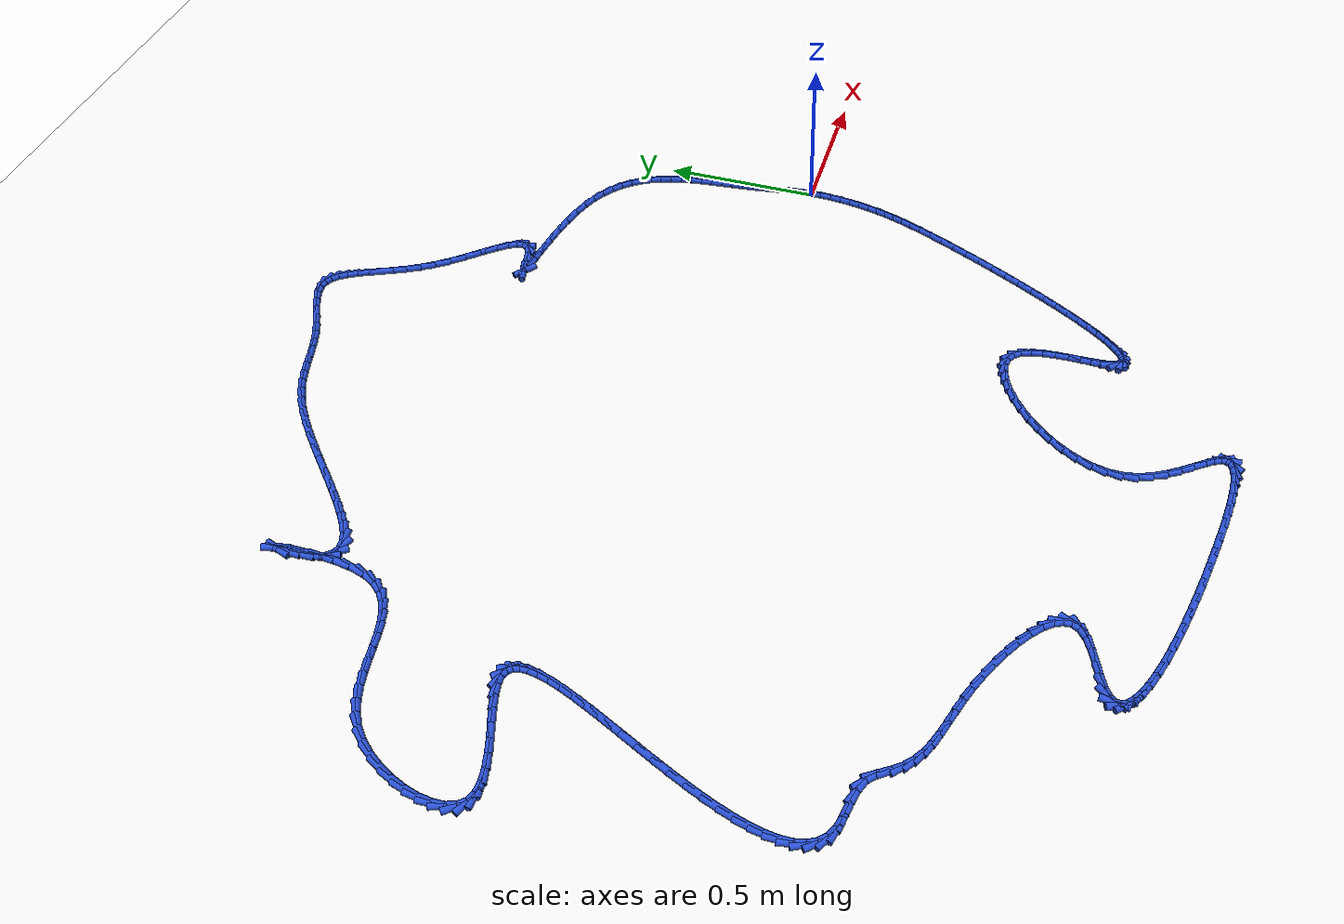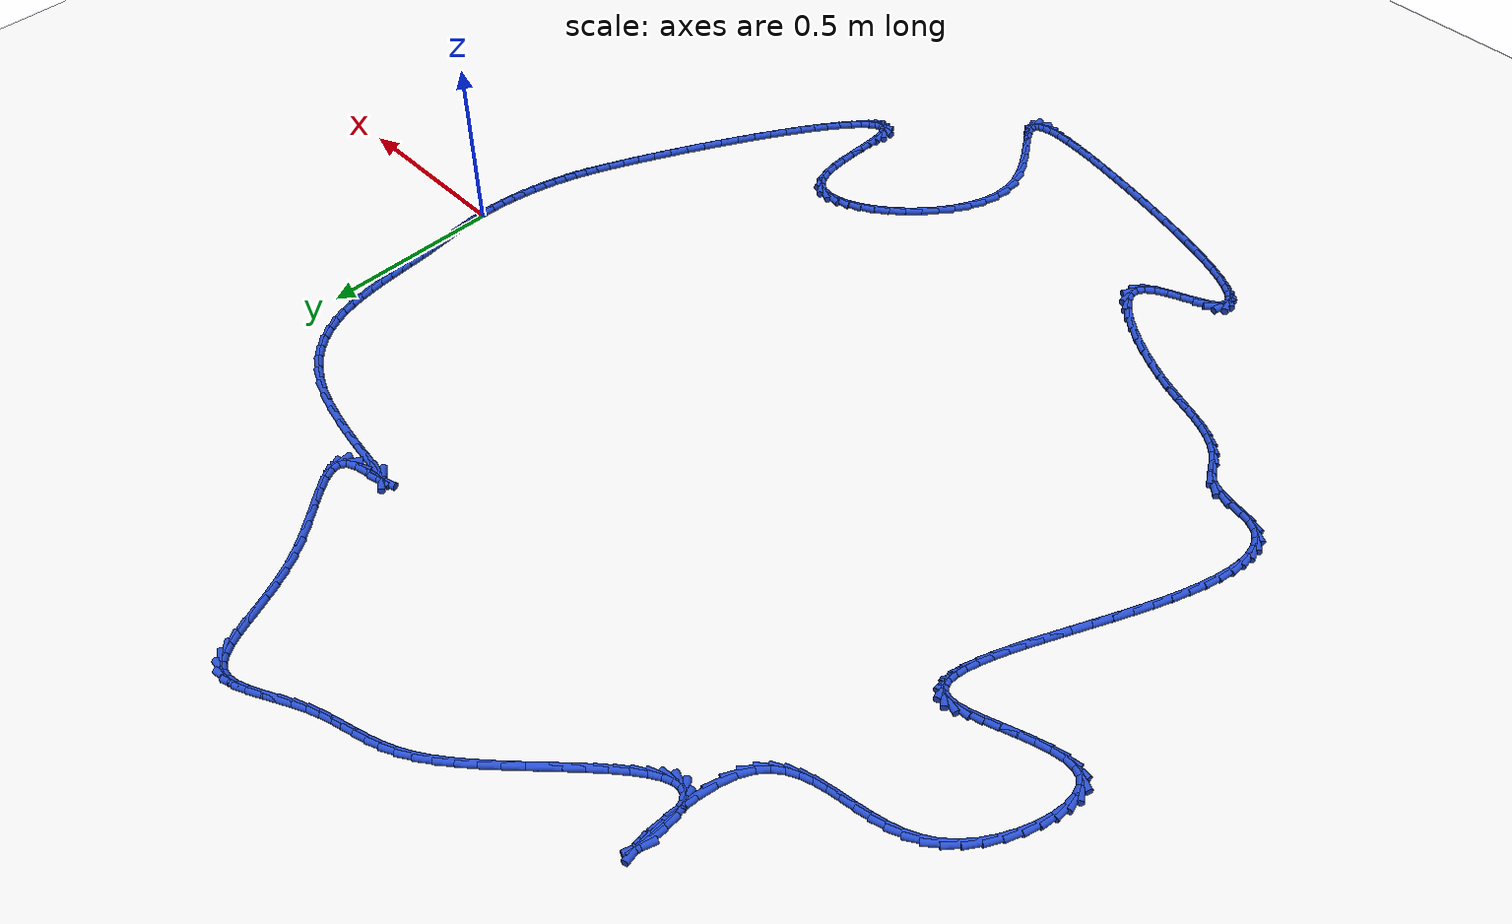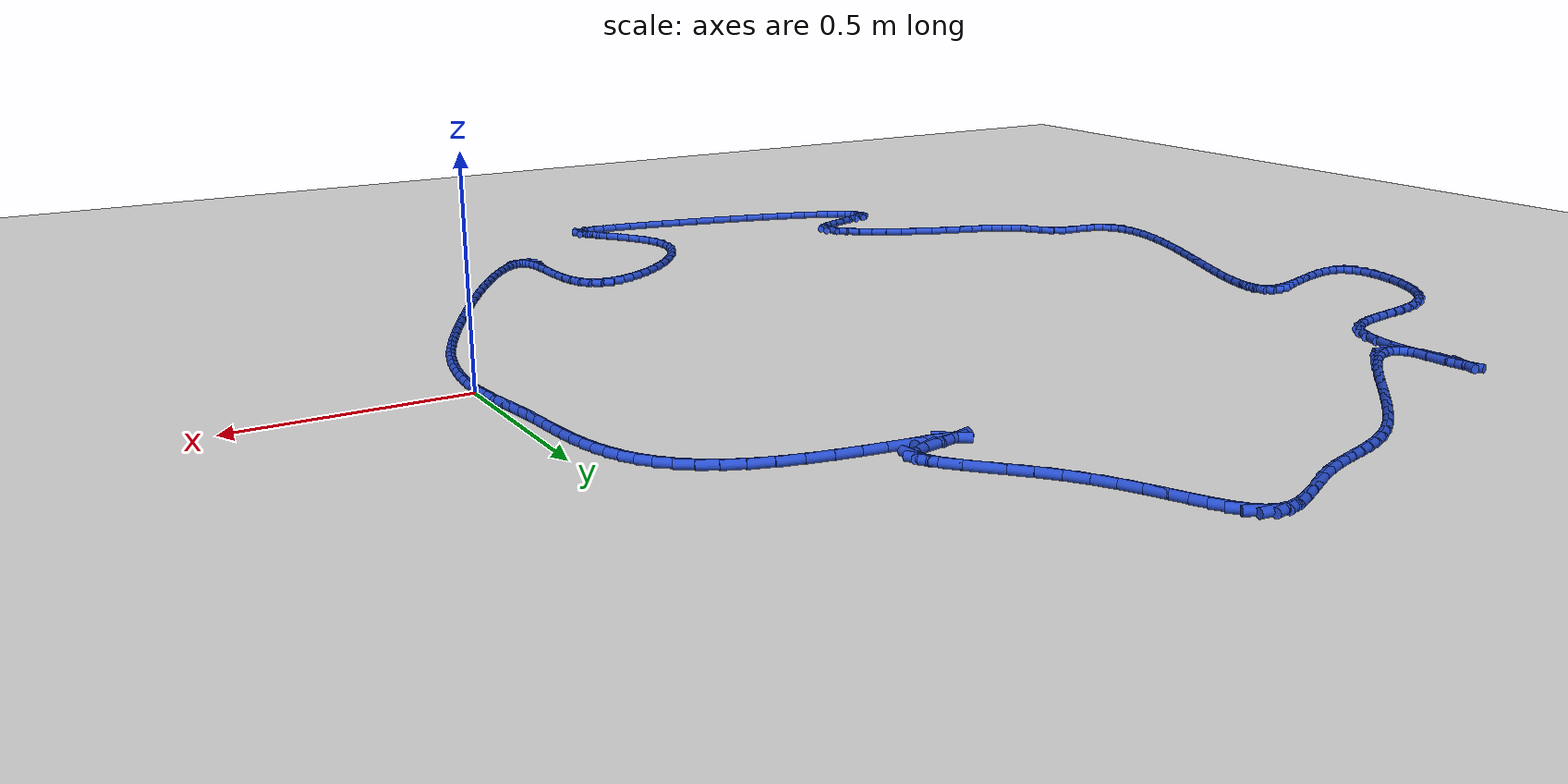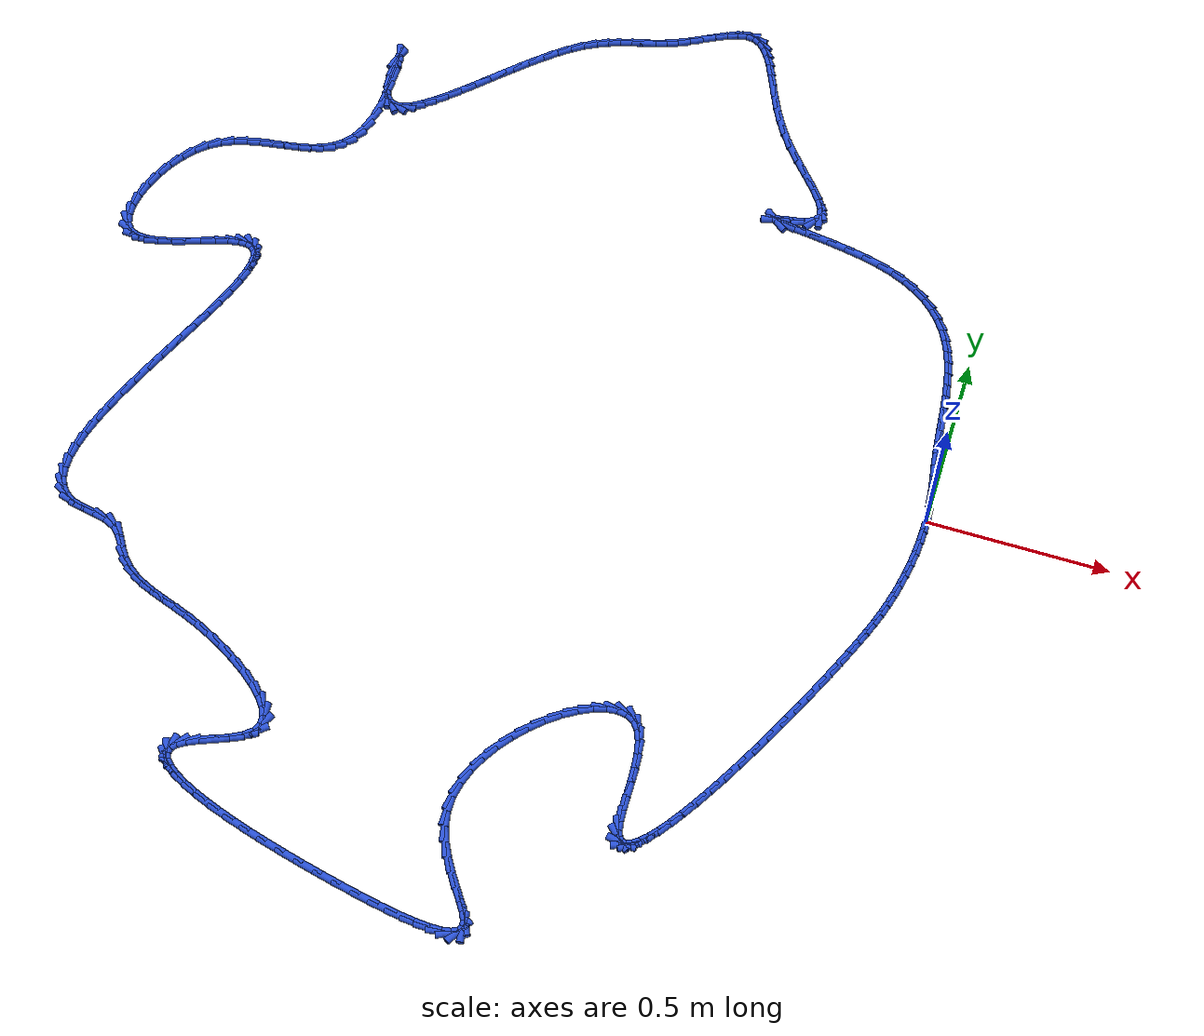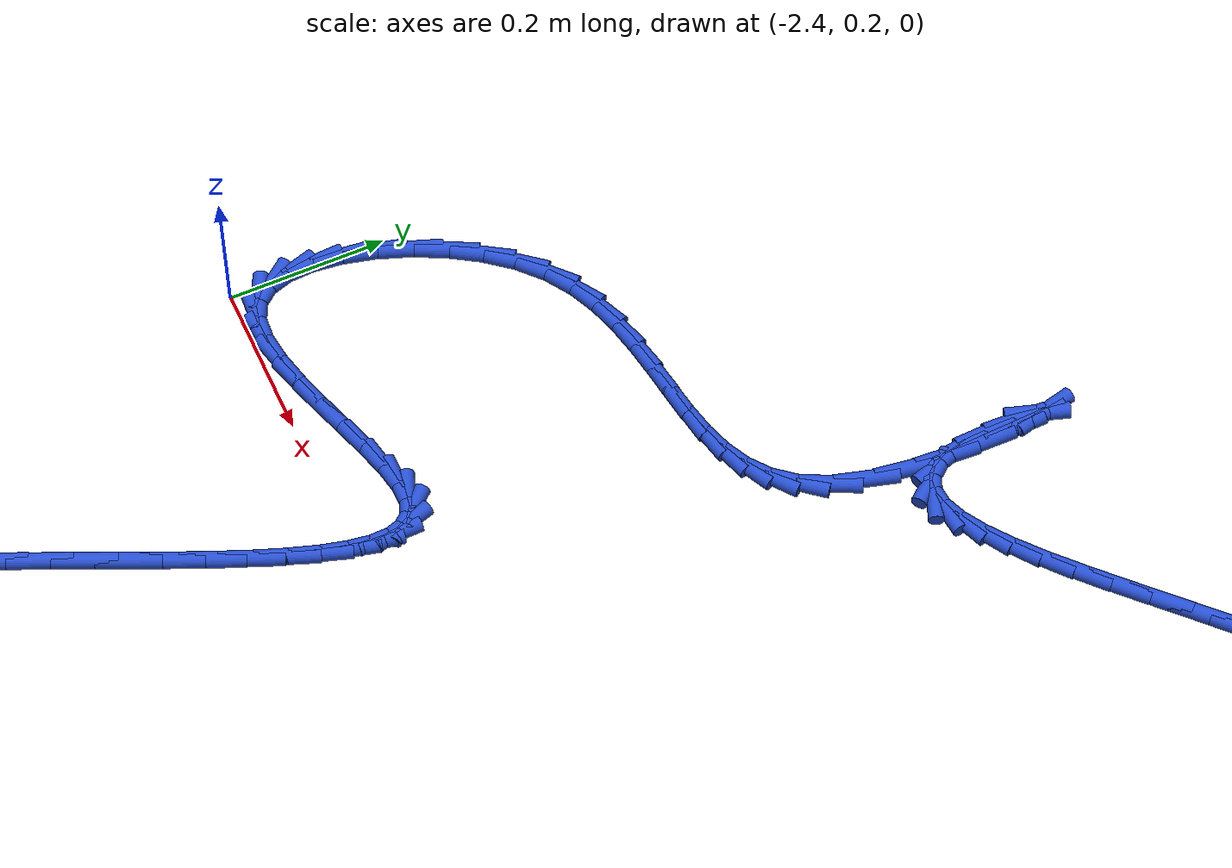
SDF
<sdf version="1.6">
 <world name="default">
  <light name="sun" type="directional">
   <pose>0 0 10 0 -0 0</pose>
   <diffuse>0.8 0.8 0.8 1</diffuse>
   <specular>0.2 0.2 0.2 1</specular>
   <attenuation>
    <range>1000</range>
    <constant>0.9</constant>
    <linear>0.01</linear>
    <quadratic>0.001</quadratic>
   </attenuation>
   <direction>-0.5 0.1 -0.9</direction>
  </light>
  <model name="ground_plane">
   <static>1</static>
   <link name="link">
    <collision name="collision">
     <geometry><plane><normal>0 0 1</normal><size>100 100</size></plane></geometry>
     <surface><friction><ode><mu>100</mu><mu2>50</mu2></ode></friction></surface>
    </collision>
    <visual name="visual">
     <cast_shadows>0</cast_shadows>
     <geometry><plane><normal>0 0 1</normal><size>100 100</size></plane></geometry>
     <material>
      <script><uri>file://media/materials/scripts/gazebo.material</uri><name>Gazebo/WhiteGlow</name></script>
     </material>
    </visual>
   </link>
  </model>
  <gravity>0 0 -9.8</gravity>
  <magnetic_field>6e-06 2.3e-05 -4.2e-05</magnetic_field>
  <atmosphere type="adiabatic"/>
  <physics name="default_physics" default="0" type="ode">
   <max_step_size>0.001</max_step_size>
   <real_time_factor>1</real_time_factor>
   <real_time_update_rate>1000</real_time_update_rate>
  </physics>
  <scene><ambient>0.4 0.4 0.4 1</ambient><background>0.7 0.7 0.7 1</background><shadows>1</shadows></scene>
  <spherical_coordinates>
   <surface_model>EARTH_WGS84</surface_model>
   <latitude_deg>0</latitude_deg>
   <longitude_deg>0</longitude_deg>
   <elevation>0</elevation>
   <heading_deg>0</heading_deg>
  </spherical_coordinates>
  <model name="line">
   <link name="link_0">
    <pose>3.469446951953614e-18 6.938893903907228e-18 0.01 0 1.57 -1.520493145179703</pose>
    <collision name="collision">
     <geometry><cylinder><radius>0.01</radius><length>0.08</length></cylinder></geometry>
    </collision>
    <visual name="visual">
     <material>
      <script><name>Gazebo/Blue</name><uri>file://media/materials/scripts/gazebo.material</uri></script>
     </material>
     <geometry><cylinder><radius>0.01</radius><length>0.08</length></cylinder></geometry>
    </visual>
   </link>
   <link name="link_1">
    <pose>-0.001735479493979407 0.03447128723011486 0.01 0 1.57 -1.479673301218593</pose>
    <collision name="collision">
     <geometry><cylinder><radius>0.01</radius><length>0.08</length></cylinder></geometry>
    </collision>
    <visual name="visual">
     <material>
      <script><name>Gazebo/Blue</name><uri>file://media/materials/scripts/gazebo.material</uri></script>
     </material>
     <geometry><cylinder><radius>0.01</radius><length>0.08</length></cylinder></geometry>
    </visual>
   </link>
   <link name="link_2">
    <pose>-0.0048575214507185546 0.06863823851478291 0.01 0 1.57 -1.4508611386593357</pose>
    <collision name="collision">
     <geometry><cylinder><radius>0.01</radius><length>0.08</length></cylinder></geometry>
    </collision>
    <visual name="visual">
     <material>
      <script><name>Gazebo/Blue</name><uri>file://media/materials/scripts/gazebo.material</uri></script>
     </material>
     <geometry><cylinder><radius>0.01</radius><length>0.08</length></cylinder></geometry>
    </visual>
   </link>
   <link name="link_3">
    <pose>-0.008958672551936508 0.10266885133756623 0.01 0 1.57 -1.4344630769436928</pose>
    <collision name="collision">
     <geometry><cylinder><radius>0.01</radius><length>0.08</length></cylinder></geometry>
    </collision>
    <visual name="visual">
     <material>
      <script><name>Gazebo/Blue</name><uri>file://media/materials/scripts/gazebo.material</uri></script>
     </material>
     <geometry><cylinder><radius>0.01</radius><length>0.08</length></cylinder></geometry>
    </visual>
   </link>
   <link name="link_4">
    <pose>-0.01363147947935231 0.1367311231820268 0.01 0 1.57 -1.4305458210199569</pose>
    <collision name="collision">
     <geometry><cylinder><radius>0.01</radius><length>0.08</length></cylinder></geometry>
    </collision>
    <visual name="visual">
     <material>
      <script><name>Gazebo/Blue</name><uri>file://media/materials/scripts/gazebo.material</uri></script>
     </material>
     <geometry><cylinder><radius>0.01</radius><length>0.08</length></cylinder></geometry>
    </visual>
   </link>
   <link name="link_5">
    <pose>-0.01846848891468505 0.17099305153172664 0.01 0 1.57 -1.4389121505210567</pose>
    <collision name="collision">
     <geometry><cylinder><radius>0.01</radius><length>0.08</length></cylinder></geometry>
    </collision>
    <visual name="visual">
     <material>
      <script><name>Gazebo/Blue</name><uri>file://media/materials/scripts/gazebo.material</uri></script>
     </material>
     <geometry><cylinder><radius>0.01</radius><length>0.08</length></cylinder></geometry>
    </visual>
   </link>
   <link name="link_6">
    <pose>-0.02306224753965377 0.2056226338702279 0.01 0 1.57 -1.458576324803985</pose>
    <collision name="collision">
     <geometry><cylinder><radius>0.01</radius><length>0.08</length></cylinder></geometry>
    </collision>
    <visual name="visual">
     <material>
      <script><name>Gazebo/Blue</name><uri>file://media/materials/scripts/gazebo.material</uri></script>
     </material>
     <geometry><cylinder><radius>0.01</radius><length>0.08</length></cylinder></geometry>
    </visual>
   </link>
   <link name="link_7">
    <pose>-0.027024161167521904 0.24077918663455944 0.01 0 1.57 -1.4773469398750507</pose>
    <collision name="collision">
     <geometry><cylinder><radius>0.01</radius><length>0.08</length></cylinder></geometry>
    </collision>
    <visual name="visual">
     <material>
      <script><name>Gazebo/Blue</name><uri>file://media/materials/scripts/gazebo.material</uri></script>
     </material>
     <geometry><cylinder><radius>0.01</radius><length>0.08</length></cylinder></geometry>
    </visual>
   </link>
   <link name="link_8">
    <pose>-0.03036615780373676 0.27643766189800995 0.01 0 1.57 -1.4843336633599877</pose>
    <collision name="collision">
     <geometry><cylinder><radius>0.01</radius><length>0.08</length></cylinder></geometry>
    </collision>
    <visual name="visual">
     <material>
      <script><name>Gazebo/Blue</name><uri>file://media/materials/scripts/gazebo.material</uri></script>
     </material>
     <geometry><cylinder><radius>0.01</radius><length>0.08</length></cylinder></geometry>
    </visual>
   </link>
   <link name="link_9">
    <pose>-0.03348304873295362 0.3123967667378714 0.01 0 1.57 -1.4794617246746493</pose>
    <collision name="collision">
     <geometry><cylinder><radius>0.01</radius><length>0.08</length></cylinder></geometry>
    </collision>
    <visual name="visual">
     <material>
      <script><name>Gazebo/Blue</name><uri>file://media/materials/scripts/gazebo.material</uri></script>
     </material>
     <geometry><cylinder><radius>0.01</radius><length>0.08</length></cylinder></geometry>
    </visual>
   </link>
   <link name="link_10">
    <pose>-0.036784974345309765 0.34844815209114216 0.01 0 1.57 -1.4627708480427988</pose>
    <collision name="collision">
     <geometry><cylinder><radius>0.01</radius><length>0.08</length></cylinder></geometry>
    </collision>
    <visual name="visual">
     <material>
      <script><name>Gazebo/Blue</name><uri>file://media/materials/scripts/gazebo.material</uri></script>
     </material>
     <geometry><cylinder><radius>0.01</radius><length>0.08</length></cylinder></geometry>
    </visual>
   </link>
   <link name="link_11">
    <pose>-0.04068207503094241 0.3843834688948197 0.01 0 1.57 -1.4339900800196281</pose>
    <collision name="collision">
     <geometry><cylinder><radius>0.01</radius><length>0.08</length></cylinder></geometry>
    </collision>
    <visual name="visual">
     <material>
      <script><name>Gazebo/Blue</name><uri>file://media/materials/scripts/gazebo.material</uri></script>
     </material>
     <geometry><cylinder><radius>0.01</radius><length>0.08</length></cylinder></geometry>
    </visual>
   </link>
   <link name="link_12">
    <pose>-0.04558449117998885 0.41999436808590285 0.01 0 1.57 -1.3925982356423274</pose>
    <collision name="collision">
     <geometry><cylinder><radius>0.01</radius><length>0.08</length></cylinder></geometry>
    </collision>
    <visual name="visual">
     <material>
      <script><name>Gazebo/Blue</name><uri>file://media/materials/scripts/gazebo.material</uri></script>
     </material>
     <geometry><cylinder><radius>0.01</radius><length>0.08</length></cylinder></geometry>
    </visual>
   </link>
   <link name="link_13">
    <pose>-0.0519023631825863 0.4550725006013891 0.01 0 1.57 -1.3379356022408442</pose>
    <collision name="collision">
     <geometry><cylinder><radius>0.01</radius><length>0.08</length></cylinder></geometry>
    </collision>
    <visual name="visual">
     <material>
      <script><name>Gazebo/Blue</name><uri>file://media/materials/scripts/gazebo.material</uri></script>
     </material>
     <geometry><cylinder><radius>0.01</radius><length>0.08</length></cylinder></geometry>
    </visual>
   </link>
   <link name="link_14">
    <pose>-0.060045831428872015 0.4894095173782768 0.01 0 1.57 -1.2693966756595008</pose>
    <collision name="collision">
     <geometry><cylinder><radius>0.01</radius><length>0.08</length></cylinder></geometry>
    </collision>
    <visual name="visual">
     <material>
      <script><name>Gazebo/Blue</name><uri>file://media/materials/scripts/gazebo.material</uri></script>
     </material>
     <geometry><cylinder><radius>0.01</radius><length>0.08</length></cylinder></geometry>
    </visual>
   </link>
   <link name="link_15">
    <pose>-0.07042503630898328 0.5227970693535642 0.01 0 1.57 -1.1867326069188164</pose>
    <collision name="collision">
     <geometry><cylinder><radius>0.01</radius><length>0.08</length></cylinder></geometry>
    </collision>
    <visual name="visual">
     <material>
      <script><name>Gazebo/Blue</name><uri>file://media/materials/scripts/gazebo.material</uri></script>
     </material>
     <geometry><cylinder><radius>0.01</radius><length>0.08</length></cylinder></geometry>
    </visual>
   </link>
   <link name="link_16">
    <pose>-0.08345011821305734 0.555026807464249 0.01 0 1.57 -1.0904602188475492</pose>
    <collision name="collision">
     <geometry><cylinder><radius>0.01</radius><length>0.08</length></cylinder></geometry>
    </collision>
    <visual name="visual">
     <material>
      <script><name>Gazebo/Blue</name><uri>file://media/materials/scripts/gazebo.material</uri></script>
     </material>
     <geometry><cylinder><radius>0.01</radius><length>0.08</length></cylinder></geometry>
    </visual>
   </link>
   <link name="link_17">
    <pose>-0.09953121753123144 0.5858903826473296 0.01 0 1.57 -0.9822924305343443</pose>
    <collision name="collision">
     <geometry><cylinder><radius>0.01</radius><length>0.08</length></cylinder></geometry>
    </collision>
    <visual name="visual">
     <material>
      <script><name>Gazebo/Blue</name><uri>file://media/materials/scripts/gazebo.material</uri></script>
     </material>
     <geometry><cylinder><radius>0.01</radius><length>0.08</length></cylinder></geometry>
    </visual>
   </link>
   <link name="link_18">
    <pose>-0.11907847465364275 0.6151794458398039 0.01 0 1.57 -0.865389421273225</pose>
    <collision name="collision">
     <geometry><cylinder><radius>0.01</radius><length>0.08</length></cylinder></geometry>
    </collision>
    <visual name="visual">
     <material>
      <script><name>Gazebo/Blue</name><uri>file://media/materials/scripts/gazebo.material</uri></script>
     </material>
     <geometry><cylinder><radius>0.01</radius><length>0.08</length></cylinder></geometry>
    </visual>
   </link>
   <link name="link_19">
    <pose>-0.14250202997042866 0.6426856479786699 0.01 0 1.57 -0.7441814541535273</pose>
    <collision name="collision">
     <geometry><cylinder><radius>0.01</radius><length>0.08</length></cylinder></geometry>
    </collision>
    <visual name="visual">
     <material>
      <script><name>Gazebo/Blue</name><uri>file://media/materials/scripts/gazebo.material</uri></script>
     </material>
     <geometry><cylinder><radius>0.01</radius><length>0.08</length></cylinder></geometry>
    </visual>
   </link>
   <link name="link_20">
    <pose>-0.17021202387172635 0.6682006400009259 0.01 0 1.57 -0.6236713893944895</pose>
    <collision name="collision">
     <geometry><cylinder><radius>0.01</radius><length>0.08</length></cylinder></geometry>
    </collision>
    <visual name="visual">
     <material>
      <script><name>Gazebo/Blue</name><uri>file://media/materials/scripts/gazebo.material</uri></script>
     </material>
     <geometry><cylinder><radius>0.01</radius><length>0.08</length></cylinder></geometry>
    </visual>
   </link>
   <link name="link_21">
    <pose>-0.2026185967476731 0.6915160728435703 0.01 0 1.57 -0.5084583369444287</pose>
    <collision name="collision">
     <geometry><cylinder><radius>0.01</radius><length>0.08</length></cylinder></geometry>
    </collision>
    <visual name="visual">
     <material>
      <script><name>Gazebo/Blue</name><uri>file://media/materials/scripts/gazebo.material</uri></script>
     </material>
     <geometry><cylinder><radius>0.01</radius><length>0.08</length></cylinder></geometry>
    </visual>
   </link>
   <link name="link_22">
    <pose>-0.2401318889884062 0.7124235974436004 0.01 0 1.57 -0.4019386086303714</pose>
    <collision name="collision">
     <geometry><cylinder><radius>0.01</radius><length>0.08</length></cylinder></geometry>
    </collision>
    <visual name="visual">
     <material>
      <script><name>Gazebo/Blue</name><uri>file://media/materials/scripts/gazebo.material</uri></script>
     </material>
     <geometry><cylinder><radius>0.01</radius><length>0.08</length></cylinder></geometry>
    </visual>
   </link>
   <link name="link_23">
    <pose>-0.2831620409840629 0.7307148647380151 0.01 0 1.57 -0.3074265537504486</pose>
    <collision name="collision">
     <geometry><cylinder><radius>0.01</radius><length>0.08</length></cylinder></geometry>
    </collision>
    <visual name="visual">
     <material>
      <script><name>Gazebo/Blue</name><uri>file://media/materials/scripts/gazebo.material</uri></script>
     </material>
     <geometry><cylinder><radius>0.01</radius><length>0.08</length></cylinder></geometry>
    </visual>
   </link>
   <link name="link_24">
    <pose>-0.3319629842435244 0.7462087898786549 0.01 0 1.57 -0.23759141025009395</pose>
    <collision name="collision">
     <geometry><cylinder><radius>0.01</radius><length>0.08</length></cylinder></geometry>
    </collision>
    <visual name="visual">
     <material>
      <script><name>Gazebo/Blue</name><uri>file://media/materials/scripts/gazebo.material</uri></script>
     </material>
     <geometry><cylinder><radius>0.01</radius><length>0.08</length></cylinder></geometry>
    </visual>
   </link>
   <link name="link_25">
    <pose>-0.3849614954309004 0.7590431939709723 0.01 0 1.57 -0.19088101204137153</pose>
    <collision name="collision">
     <geometry><cylinder><radius>0.01</radius><length>0.08</length></cylinder></geometry>
    </collision>
    <visual name="visual">
     <material>
      <script><name>Gazebo/Blue</name><uri>file://media/materials/scripts/gazebo.material</uri></script>
     </material>
     <geometry><cylinder><radius>0.01</radius><length>0.08</length></cylinder></geometry>
    </visual>
   </link>
   <link name="link_26">
    <pose>-0.43940018881852533 0.7695625781606259 0.01 0 1.57 -0.15968537976516559</pose>
    <collision name="collision">
     <geometry><cylinder><radius>0.01</radius><length>0.08</length></cylinder></geometry>
    </collision>
    <visual name="visual">
     <material>
      <script><name>Gazebo/Blue</name><uri>file://media/materials/scripts/gazebo.material</uri></script>
     </material>
     <geometry><cylinder><radius>0.01</radius><length>0.08</length></cylinder></geometry>
    </visual>
   </link>
   <link name="link_27">
    <pose>-0.49250170075054456 0.7781149304790502 0.01 0 1.57 -0.14059987725914058</pose>
    <collision name="collision">
     <geometry><cylinder><radius>0.01</radius><length>0.08</length></cylinder></geometry>
    </collision>
    <visual name="visual">
     <material>
      <script><name>Gazebo/Blue</name><uri>file://media/materials/scripts/gazebo.material</uri></script>
     </material>
     <geometry><cylinder><radius>0.01</radius><length>0.08</length></cylinder></geometry>
    </visual>
   </link>
   <link name="link_28">
    <pose>-0.5414886675711043 0.7850482389576805 0.01 0 1.57 -0.1337085500804472</pose>
    <collision name="collision">
     <geometry><cylinder><radius>0.01</radius><length>0.08</length></cylinder></geometry>
    </collision>
    <visual name="visual">
     <material>
      <script><name>Gazebo/Blue</name><uri>file://media/materials/scripts/gazebo.material</uri></script>
     </material>
     <geometry><cylinder><radius>0.01</radius><length>0.08</length></cylinder></geometry>
    </visual>
   </link>
   <link name="link_29">
    <pose>-0.5835837256243501 0.7907104916279513 0.01 0 1.57 -0.14512727659500194</pose>
    <collision name="collision">
     <geometry><cylinder><radius>0.01</radius><length>0.08</length></cylinder></geometry>
    </collision>
    <visual name="visual">
     <material>
      <script><name>Gazebo/Blue</name><uri>file://media/materials/scripts/gazebo.material</uri></script>
     </material>
     <geometry><cylinder><radius>0.01</radius><length>0.08</length></cylinder></geometry>
    </visual>
   </link>
   <link name="link_30">
    <pose>-0.6160095112544279 0.7954496765212976 0.01 0 1.57 -0.20548088603850004</pose>
    <collision name="collision">
     <geometry><cylinder><radius>0.01</radius><length>0.08</length></cylinder></geometry>
    </collision>
    <visual name="visual">
     <material>
      <script><name>Gazebo/Blue</name><uri>file://media/materials/scripts/gazebo.material</uri></script>
     </material>
     <geometry><cylinder><radius>0.01</radius><length>0.08</length></cylinder></geometry>
    </visual>
   </link>
   <link name="link_31">
    <pose>-0.6359886608054834 0.7996137816691546 0.01 0 1.57 -0.691551199999225</pose>
    <collision name="collision">
     <geometry><cylinder><radius>0.01</radius><length>0.08</length></cylinder></geometry>
    </collision>
    <visual name="visual">
     <material>
      <script><name>Gazebo/Blue</name><uri>file://media/materials/scripts/gazebo.material</uri></script>
     </material>
     <geometry><cylinder><radius>0.01</radius><length>0.08</length></cylinder></geometry>
    </visual>
   </link>
   <link name="link_32">
    <pose>-0.6407438106216622 0.8035507951029567 0.01 0 1.57 0.29726757542603127</pose>
    <collision name="collision">
     <geometry><cylinder><radius>0.01</radius><length>0.08</length></cylinder></geometry>
    </collision>
    <visual name="visual">
     <material>
      <script><name>Gazebo/Blue</name><uri>file://media/materials/scripts/gazebo.material</uri></script>
     </material>
     <geometry><cylinder><radius>0.01</radius><length>0.08</length></cylinder></geometry>
    </visual>
   </link>
   <link name="link_33">
    <pose>-0.6274975970471104 0.8076087048541392 0.01 0 1.57 0.15230203504884007</pose>
    <collision name="collision">
     <geometry><cylinder><radius>0.01</radius><length>0.08</length></cylinder></geometry>
    </collision>
    <visual name="visual">
     <material>
      <script><name>Gazebo/Blue</name><uri>file://media/materials/scripts/gazebo.material</uri></script>
     </material>
     <geometry><cylinder><radius>0.01</radius><length>0.08</length></cylinder></geometry>
    </visual>
   </link>
   <link name="link_34">
    <pose>-0.5961950611726069 0.8124133517301196 0.01 0 1.57 0.19830524384770448</pose>
    <collision name="collision">
     <geometry><cylinder><radius>0.01</radius><length>0.08</length></cylinder></geometry>
    </collision>
    <visual name="visual">
     <material>
      <script><name>Gazebo/Blue</name><uri>file://media/materials/scripts/gazebo.material</uri></script>
     </material>
     <geometry><cylinder><radius>0.01</radius><length>0.08</length></cylinder></geometry>
    </visual>
   </link>
   <link name="link_35">
    <pose>-0.5591647422391702 0.8198544552255956 0.01 0 1.57 0.42213728435637043</pose>
    <collision name="collision">
     <geometry><cylinder><radius>0.01</radius><length>0.08</length></cylinder></geometry>
    </collision>
    <visual name="visual">
     <material>
      <script><name>Gazebo/Blue</name><uri>file://media/materials/scripts/gazebo.material</uri></script>
     </material>
     <geometry><cylinder><radius>0.01</radius><length>0.08</length></cylinder></geometry>
    </visual>
   </link>
   <link name="link_36">
    <pose>-0.531856524955483 0.8321196274092257 0.01 0 1.57 1.0169095133444517</pose>
    <collision name="collision">
     <geometry><cylinder><radius>0.01</radius><length>0.08</length></cylinder></geometry>
    </collision>
    <visual name="visual">
     <material>
      <script><name>Gazebo/Blue</name><uri>file://media/materials/scripts/gazebo.material</uri></script>
     </material>
     <geometry><cylinder><radius>0.01</radius><length>0.08</length></cylinder></geometry>
    </visual>
   </link>
   <link name="link_37">
    <pose>-0.5207856084372138 0.8500202375938648 0.01 0 1.57 -1.4468187485999842</pose>
    <collision name="collision">
     <geometry><cylinder><radius>0.01</radius><length>0.08</length></cylinder></geometry>
    </collision>
    <visual name="visual">
     <material>
      <script><name>Gazebo/Blue</name><uri>file://media/materials/scripts/gazebo.material</uri></script>
     </material>
     <geometry><cylinder><radius>0.01</radius><length>0.08</length></cylinder></geometry>
    </visual>
   </link>
   <link name="link_38">
    <pose>-0.5236504663556029 0.8730095946627591 0.01 0 1.57 -1.095914336050709</pose>
    <collision name="collision">
     <geometry><cylinder><radius>0.01</radius><length>0.08</length></cylinder></geometry>
    </collision>
    <visual name="visual">
     <material>
      <script><name>Gazebo/Blue</name><uri>file://media/materials/scripts/gazebo.material</uri></script>
     </material>
     <geometry><cylinder><radius>0.01</radius><length>0.08</length></cylinder></geometry>
    </visual>
   </link>
   <link name="link_39">
    <pose>-0.5377753619319126 0.9004833670057931 0.01 0 1.57 -0.9439555136868737</pose>
    <collision name="collision">
     <geometry><cylinder><radius>0.01</radius><length>0.08</length></cylinder></geometry>
    </collision>
    <visual name="visual">
     <material>
      <script><name>Gazebo/Blue</name><uri>file://media/materials/scripts/gazebo.material</uri></script>
     </material>
     <geometry><cylinder><radius>0.01</radius><length>0.08</length></cylinder></geometry>
    </visual>
   </link>
   <link name="link_40">
    <pose>-0.5604845583874049 0.9318372230128507 0.01 0 1.57 -0.8801663626201262</pose>
    <collision name="collision">
     <geometry><cylinder><radius>0.01</radius><length>0.08</length></cylinder></geometry>
    </collision>
    <visual name="visual">
     <material>
      <script><name>Gazebo/Blue</name><uri>file://media/materials/scripts/gazebo.material</uri></script>
     </material>
     <geometry><cylinder><radius>0.01</radius><length>0.08</length></cylinder></geometry>
    </visual>
   </link>
   <link name="link_41">
    <pose>-0.5891023189433426 0.9664668310738164 0.01 0 1.57 -0.8640542533962889</pose>
    <collision name="collision">
     <geometry><cylinder><radius>0.01</radius><length>0.08</length></cylinder></geometry>
    </collision>
    <visual name="visual">
     <material>
      <script><name>Gazebo/Blue</name><uri>file://media/materials/scripts/gazebo.material</uri></script>
     </material>
     <geometry><cylinder><radius>0.01</radius><length>0.08</length></cylinder></geometry>
    </visual>
   </link>
   <link name="link_42">
    <pose>-0.6209529068209878 1.0037678595785737 0.01 0 1.57 -0.8820706175119707</pose>
    <collision name="collision">
     <geometry><cylinder><radius>0.01</radius><length>0.08</length></cylinder></geometry>
    </collision>
    <visual name="visual">
     <material>
      <script><name>Gazebo/Blue</name><uri>file://media/materials/scripts/gazebo.material</uri></script>
     </material>
     <geometry><cylinder><radius>0.01</radius><length>0.08</length></cylinder></geometry>
    </visual>
   </link>
   <link name="link_43">
    <pose>-0.6533605852416028 1.0431359769170072 0.01 0 1.57 -0.932552775636398</pose>
    <collision name="collision">
     <geometry><cylinder><radius>0.01</radius><length>0.08</length></cylinder></geometry>
    </collision>
    <visual name="visual">
     <material>
      <script><name>Gazebo/Blue</name><uri>file://media/materials/scripts/gazebo.material</uri></script>
     </material>
     <geometry><cylinder><radius>0.01</radius><length>0.08</length></cylinder></geometry>
    </visual>
   </link>
   <link name="link_44">
    <pose>-0.6836496318088999 1.0839668504136462 0.01 0 1.57 -1.0104647603875268</pose>
    <collision name="collision">
     <geometry><cylinder><radius>0.01</radius><length>0.08</length></cylinder></geometry>
    </collision>
    <visual name="visual">
     <material>
      <script><name>Gazebo/Blue</name><uri>file://media/materials/scripts/gazebo.material</uri></script>
     </material>
     <geometry><cylinder><radius>0.01</radius><length>0.08</length></cylinder></geometry>
    </visual>
   </link>
   <link name="link_45">
    <pose>-0.7097765928634499 1.1256093131634963 0.01 0 1.57 -1.0801747191157425</pose>
    <collision name="collision">
     <geometry><cylinder><radius>0.01</radius><length>0.08</length></cylinder></geometry>
    </collision>
    <visual name="visual">
     <material>
      <script><name>Gazebo/Blue</name><uri>file://media/materials/scripts/gazebo.material</uri></script>
     </material>
     <geometry><cylinder><radius>0.01</radius><length>0.08</length></cylinder></geometry>
    </visual>
   </link>
   <link name="link_46">
    <pose>-0.7320154467210744 1.1672405384360778 0.01 0 1.57 -1.1314485764993383</pose>
    <collision name="collision">
     <geometry><cylinder><radius>0.01</radius><length>0.08</length></cylinder></geometry>
    </collision>
    <visual name="visual">
     <material>
      <script><name>Gazebo/Blue</name><uri>file://media/materials/scripts/gazebo.material</uri></script>
     </material>
     <geometry><cylinder><radius>0.01</radius><length>0.08</length></cylinder></geometry>
    </visual>
   </link>
   <link name="link_47">
    <pose>-0.7511709789504042 1.2079983808579642 0.01 0 1.57 -1.162593641508173</pose>
    <collision name="collision">
     <geometry><cylinder><radius>0.01</radius><length>0.08</length></cylinder></geometry>
    </collision>
    <visual name="visual">
     <material>
      <script><name>Gazebo/Blue</name><uri>file://media/materials/scripts/gazebo.material</uri></script>
     </material>
     <geometry><cylinder><radius>0.01</radius><length>0.08</length></cylinder></geometry>
    </visual>
   </link>
   <link name="link_48">
    <pose>-0.7680479751200701 1.2470206950557308 0.01 0 1.57 -1.1707228555279066</pose>
    <collision name="collision">
     <geometry><cylinder><radius>0.01</radius><length>0.08</length></cylinder></geometry>
    </collision>
    <visual name="visual">
     <material>
      <script><name>Gazebo/Blue</name><uri>file://media/materials/scripts/gazebo.material</uri></script>
     </material>
     <geometry><cylinder><radius>0.01</radius><length>0.08</length></cylinder></geometry>
    </visual>
   </link>
   <link name="link_49">
    <pose>-0.7834512207987024 1.2834453356559512 0.01 0 1.57 -1.150465146954721</pose>
    <collision name="collision">
     <geometry><cylinder><radius>0.01</radius><length>0.08</length></cylinder></geometry>
    </collision>
    <visual name="visual">
     <material>
      <script><name>Gazebo/Blue</name><uri>file://media/materials/scripts/gazebo.material</uri></script>
     </material>
     <geometry><cylinder><radius>0.01</radius><length>0.08</length></cylinder></geometry>
    </visual>
   </link>
   <link name="link_50">
    <pose>-0.7981855015549317 1.3164101572851996 0.01 0 1.57 -1.091941891874106</pose>
    <collision name="collision">
     <geometry><cylinder><radius>0.01</radius><length>0.08</length></cylinder></geometry>
    </collision>
    <visual name="visual">
     <material>
      <script><name>Gazebo/Blue</name><uri>file://media/materials/scripts/gazebo.material</uri></script>
     </material>
     <geometry><cylinder><radius>0.01</radius><length>0.08</length></cylinder></geometry>
    </visual>
   </link>
   <link name="link_51">
    <pose>-0.813055602957389 1.345053014570051 0.01 0 1.57 -0.9777482804261196</pose>
    <collision name="collision">
     <geometry><cylinder><radius>0.01</radius><length>0.08</length></cylinder></geometry>
    </collision>
    <visual name="visual">
     <material>
      <script><name>Gazebo/Blue</name><uri>file://media/materials/scripts/gazebo.material</uri></script>
     </material>
     <geometry><cylinder><radius>0.01</radius><length>0.08</length></cylinder></geometry>
    </visual>
   </link>
   <link name="link_52">
    <pose>-0.8288663105747046 1.3685117621370786 0.01 0 1.57 -0.7812914461977593</pose>
    <collision name="collision">
     <geometry><cylinder><radius>0.01</radius><length>0.08</length></cylinder></geometry>
    </collision>
    <visual name="visual">
     <material>
      <script><name>Gazebo/Blue</name><uri>file://media/materials/scripts/gazebo.material</uri></script>
     </material>
     <geometry><cylinder><radius>0.01</radius><length>0.08</length></cylinder></geometry>
    </visual>
   </link>
   <link name="link_53">
    <pose>-0.8464224099755095 1.3859242546128578 0.01 0 1.57 -0.4814289942595881</pose>
    <collision name="collision">
     <geometry><cylinder><radius>0.01</radius><length>0.08</length></cylinder></geometry>
    </collision>
    <visual name="visual">
     <material>
      <script><name>Gazebo/Blue</name><uri>file://media/materials/scripts/gazebo.material</uri></script>
     </material>
     <geometry><cylinder><radius>0.01</radius><length>0.08</length></cylinder></geometry>
    </visual>
   </link>
   <link name="link_54">
    <pose>-0.8665286867284341 1.3964283466239622 0.01 0 1.57 -0.11603698721816989</pose>
    <collision name="collision">
     <geometry><cylinder><radius>0.01</radius><length>0.08</length></cylinder></geometry>
    </collision>
    <visual name="visual">
     <material>
      <script><name>Gazebo/Blue</name><uri>file://media/materials/scripts/gazebo.material</uri></script>
     </material>
     <geometry><cylinder><radius>0.01</radius><length>0.08</length></cylinder></geometry>
    </visual>
   </link>
   <link name="link_55">
    <pose>-0.889989327332415 1.399162933063862 0.01 0 1.57 0.18880216271722802</pose>
    <collision name="collision">
     <geometry><cylinder><radius>0.01</radius><length>0.08</length></cylinder></geometry>
    </collision>
    <visual name="visual">
     <material>
      <script><name>Gazebo/Blue</name><uri>file://media/materials/scripts/gazebo.material</uri></script>
     </material>
     <geometry><cylinder><radius>0.01</radius><length>0.08</length></cylinder></geometry>
    </visual>
   </link>
   <link name="link_56">
    <pose>-0.9172082284286742 1.3939620003850794 0.01 0 1.57 0.36009215054816684</pose>
    <collision name="collision">
     <geometry><cylinder><radius>0.01</radius><length>0.08</length></cylinder></geometry>
    </collision>
    <visual name="visual">
     <material>
      <script><name>Gazebo/Blue</name><uri>file://media/materials/scripts/gazebo.material</uri></script>
     </material>
     <geometry><cylinder><radius>0.01</radius><length>0.08</length></cylinder></geometry>
    </visual>
   </link>
   <link name="link_57">
    <pose>-0.947495694794874 1.382558525131339 0.01 0 1.57 0.4465359171212403</pose>
    <collision name="collision">
     <geometry><cylinder><radius>0.01</radius><length>0.08</length></cylinder></geometry>
    </collision>
    <visual name="visual">
     <material>
      <script><name>Gazebo/Blue</name><uri>file://media/materials/scripts/gazebo.material</uri></script>
     </material>
     <geometry><cylinder><radius>0.01</radius><length>0.08</length></cylinder></geometry>
    </visual>
   </link>
   <link name="link_58">
    <pose>-0.9799769818239045 1.3670068166577853 0.01 0 1.57 0.481135154921002</pose>
    <collision name="collision">
     <geometry><cylinder><radius>0.01</radius><length>0.08</length></cylinder></geometry>
    </collision>
    <visual name="visual">
     <material>
      <script><name>Gazebo/Blue</name><uri>file://media/materials/scripts/gazebo.material</uri></script>
     </material>
     <geometry><cylinder><radius>0.01</radius><length>0.08</length></cylinder></geometry>
    </visual>
   </link>
   <link name="link_59">
    <pose>-1.013777344908657 1.3493611843195648 0.01 0 1.57 0.47671102504164</pose>
    <collision name="collision">
     <geometry><cylinder><radius>0.01</radius><length>0.08</length></cylinder></geometry>
    </collision>
    <visual name="visual">
     <material>
      <script><name>Gazebo/Blue</name><uri>file://media/materials/scripts/gazebo.material</uri></script>
     </material>
     <geometry><cylinder><radius>0.01</radius><length>0.08</length></cylinder></geometry>
    </visual>
   </link>
   <link name="link_60">
    <pose>-1.0480220394420212 1.3316759374718221 0.01 0 1.57 0.43407448732028986</pose>
    <collision name="collision">
     <geometry><cylinder><radius>0.01</radius><length>0.08</length></cylinder></geometry>
    </collision>
    <visual name="visual">
     <material>
      <script><name>Gazebo/Blue</name><uri>file://media/materials/scripts/gazebo.material</uri></script>
     </material>
     <geometry><cylinder><radius>0.01</radius><length>0.08</length></cylinder></geometry>
    </visual>
   </link>
   <link name="link_61">
    <pose>-1.0818383477080278 1.315999989730625 0.01 0 1.57 0.364332486926034</pose>
    <collision name="collision">
     <geometry><cylinder><radius>0.01</radius><length>0.08</length></cylinder></geometry>
    </collision>
    <visual name="visual">
     <material>
      <script><name>Gazebo/Blue</name><uri>file://media/materials/scripts/gazebo.material</uri></script>
     </material>
     <geometry><cylinder><radius>0.01</radius><length>0.08</length></cylinder></geometry>
    </visual>
   </link>
   <link name="link_62">
    <pose>-1.1146965028481075 1.3034692933261747 0.01 0 1.57 0.30722305614795414</pose>
    <collision name="collision">
     <geometry><cylinder><radius>0.01</radius><length>0.08</length></cylinder></geometry>
    </collision>
    <visual name="visual">
     <material>
      <script><name>Gazebo/Blue</name><uri>file://media/materials/scripts/gazebo.material</uri></script>
     </material>
     <geometry><cylinder><radius>0.01</radius><length>0.08</length></cylinder></geometry>
    </visual>
   </link>
   <link name="link_63">
    <pose>-1.1467931468735109 1.2932860445753274 0.01 0 1.57 0.27374645443688667</pose>
    <collision name="collision">
     <geometry><cylinder><radius>0.01</radius><length>0.08</length></cylinder></geometry>
    </collision>
    <visual name="visual">
     <material>
      <script><name>Gazebo/Blue</name><uri>file://media/materials/scripts/gazebo.material</uri></script>
     </material>
     <geometry><cylinder><radius>0.01</radius><length>0.08</length></cylinder></geometry>
    </visual>
   </link>
   <link name="link_64">
    <pose>-1.1784174702246566 1.2844060688052383 0.01 0 1.57 0.267613499157372</pose>
    <collision name="collision">
     <geometry><cylinder><radius>0.01</radius><length>0.08</length></cylinder></geometry>
    </collision>
    <visual name="visual">
     <material>
      <script><name>Gazebo/Blue</name><uri>file://media/materials/scripts/gazebo.material</uri></script>
     </material>
     <geometry><cylinder><radius>0.01</radius><length>0.08</length></cylinder></geometry>
    </visual>
   </link>
   <link name="link_65">
    <pose>-1.2098586633419663 1.275785191343063 0.01 0 1.57 0.2897627665020422</pose>
    <collision name="collision">
     <geometry><cylinder><radius>0.01</radius><length>0.08</length></cylinder></geometry>
    </collision>
    <visual name="visual">
     <material>
      <script><name>Gazebo/Blue</name><uri>file://media/materials/scripts/gazebo.material</uri></script>
     </material>
     <geometry><cylinder><radius>0.01</radius><length>0.08</length></cylinder></geometry>
    </visual>
   </link>
   <link name="link_66">
    <pose>-1.2414059166658609 1.2663792375159564 0.01 0 1.57 0.3382170828029676</pose>
    <collision name="collision">
     <geometry><cylinder><radius>0.01</radius><length>0.08</length></cylinder></geometry>
    </collision>
    <visual name="visual">
     <material>
      <script><name>Gazebo/Blue</name><uri>file://media/materials/scripts/gazebo.material</uri></script>
     </material>
     <geometry><cylinder><radius>0.01</radius><length>0.08</length></cylinder></geometry>
    </visual>
   </link>
   <link name="link_67">
    <pose>-1.2733484206367605 1.2551440326510734 0.01 0 1.57 0.4081408761389661</pose>
    <collision name="collision">
     <geometry><cylinder><radius>0.01</radius><length>0.08</length></cylinder></geometry>
    </collision>
    <visual name="visual">
     <material>
      <script><name>Gazebo/Blue</name><uri>file://media/materials/scripts/gazebo.material</uri></script>
     </material>
     <geometry><cylinder><radius>0.01</radius><length>0.08</length></cylinder></geometry>
    </visual>
   </link>
   <link name="link_68">
    <pose>-1.3059753656950859 1.2410354020755698 0.01 0 1.57 0.49240842649528743</pose>
    <collision name="collision">
     <geometry><cylinder><radius>0.01</radius><length>0.08</length></cylinder></geometry>
    </collision>
    <visual name="visual">
     <material>
      <script><name>Gazebo/Blue</name><uri>file://media/materials/scripts/gazebo.material</uri></script>
     </material>
     <geometry><cylinder><radius>0.01</radius><length>0.08</length></cylinder></geometry>
    </visual>
   </link>
   <link name="link_69">
    <pose>-1.3395759422812579 1.2230091711166013 0.01 0 1.57 0.581598620034394</pose>
    <collision name="collision">
     <geometry><cylinder><radius>0.01</radius><length>0.08</length></cylinder></geometry>
    </collision>
    <visual name="visual">
     <material>
      <script><name>Gazebo/Blue</name><uri>file://media/materials/scripts/gazebo.material</uri></script>
     </material>
     <geometry><cylinder><radius>0.01</radius><length>0.08</length></cylinder></geometry>
    </visual>
   </link>
   <link name="link_70">
    <pose>-1.3744132595093408 1.2001051794795756 0.01 0 1.57 0.654143767855493</pose>
    <collision name="collision">
     <geometry><cylinder><radius>0.01</radius><length>0.08</length></cylinder></geometry>
    </collision>
    <visual name="visual">
     <material>
      <script><name>Gazebo/Blue</name><uri>file://media/materials/scripts/gazebo.material</uri></script>
     </material>
     <geometry><cylinder><radius>0.01</radius><length>0.08</length></cylinder></geometry>
    </visual>
   </link>
   <link name="link_71">
    <pose>-1.410391941260637 1.1725180361301792 0.01 0 1.57 0.7042863489053723</pose>
    <collision name="collision">
     <geometry><cylinder><radius>0.01</radius><length>0.08</length></cylinder></geometry>
    </collision>
    <visual name="visual">
     <material>
      <script><name>Gazebo/Blue</name><uri>file://media/materials/scripts/gazebo.material</uri></script>
     </material>
     <geometry><cylinder><radius>0.01</radius><length>0.08</length></cylinder></geometry>
    </visual>
   </link>
   <link name="link_72">
    <pose>-1.4471560446689522 1.1412816997276407 0.01 0 1.57 0.7381925651348835</pose>
    <collision name="collision">
     <geometry><cylinder><radius>0.01</radius><length>0.08</length></cylinder></geometry>
    </collision>
    <visual name="visual">
     <material>
      <script><name>Gazebo/Blue</name><uri>file://media/materials/scripts/gazebo.material</uri></script>
     </material>
     <geometry><cylinder><radius>0.01</radius><length>0.08</length></cylinder></geometry>
    </visual>
   </link>
   <link name="link_73">
    <pose>-1.4843437562049615 1.1074490397835797 0.01 0 1.57 0.7596086856630443</pose>
    <collision name="collision">
     <geometry><cylinder><radius>0.01</radius><length>0.08</length></cylinder></geometry>
    </collision>
    <visual name="visual">
     <material>
      <script><name>Gazebo/Blue</name><uri>file://media/materials/scripts/gazebo.material</uri></script>
     </material>
     <geometry><cylinder><radius>0.01</radius><length>0.08</length></cylinder></geometry>
    </visual>
   </link>
   <link name="link_74">
    <pose>-1.52159326233934 1.0720729258096189 0.01 0 1.57 0.7705290940824102</pose>
    <collision name="collision">
     <geometry><cylinder><radius>0.01</radius><length>0.08</length></cylinder></geometry>
    </collision>
    <visual name="visual">
     <material>
      <script><name>Gazebo/Blue</name><uri>file://media/materials/scripts/gazebo.material</uri></script>
     </material>
     <geometry><cylinder><radius>0.01</radius><length>0.08</length></cylinder></geometry>
    </visual>
   </link>
   <link name="link_75">
    <pose>-1.5585427495427622 1.0362062273173764 0.01 0 1.57 0.7716650857625963</pose>
    <collision name="collision">
     <geometry><cylinder><radius>0.01</radius><length>0.08</length></cylinder></geometry>
    </collision>
    <visual name="visual">
     <material>
      <script><name>Gazebo/Blue</name><uri>file://media/materials/scripts/gazebo.material</uri></script>
     </material>
     <geometry><cylinder><radius>0.01</radius><length>0.08</length></cylinder></geometry>
    </visual>
   </link>
   <link name="link_76">
    <pose>-1.5948304042859038 1.000901813818474 0.01 0 1.57 0.7625642047551838</pose>
    <collision name="collision">
     <geometry><cylinder><radius>0.01</radius><length>0.08</length></cylinder></geometry>
    </collision>
    <visual name="visual">
     <material>
      <script><name>Gazebo/Blue</name><uri>file://media/materials/scripts/gazebo.material</uri></script>
     </material>
     <geometry><cylinder><radius>0.01</radius><length>0.08</length></cylinder></geometry>
    </visual>
   </link>
   <link name="link_77">
    <pose>-1.6300944130394397 0.9672125548245311 0.01 0 1.57 0.7414000162682713</pose>
    <collision name="collision">
     <geometry><cylinder><radius>0.01</radius><length>0.08</length></cylinder></geometry>
    </collision>
    <visual name="visual">
     <material>
      <script><name>Gazebo/Blue</name><uri>file://media/materials/scripts/gazebo.material</uri></script>
     </material>
     <geometry><cylinder><radius>0.01</radius><length>0.08</length></cylinder></geometry>
    </visual>
   </link>
   <link name="link_78">
    <pose>-1.6639729622740456 0.9361913198471674 0.01 0 1.57 0.7042908837811375</pose>
    <collision name="collision">
     <geometry><cylinder><radius>0.01</radius><length>0.08</length></cylinder></geometry>
    </collision>
    <visual name="visual">
     <material>
      <script><name>Gazebo/Blue</name><uri>file://media/materials/scripts/gazebo.material</uri></script>
     </material>
     <geometry><cylinder><radius>0.01</radius><length>0.08</length></cylinder></geometry>
    </visual>
   </link>
   <link name="link_79">
    <pose>-1.6961042384603948 0.9088909783980047 0.01 0 1.57 0.6437128908015034</pose>
    <collision name="collision">
     <geometry><cylinder><radius>0.01</radius><length>0.08</length></cylinder></geometry>
    </collision>
    <visual name="visual">
     <material>
      <script><name>Gazebo/Blue</name><uri>file://media/materials/scripts/gazebo.material</uri></script>
     </material>
     <geometry><cylinder><radius>0.01</radius><length>0.08</length></cylinder></geometry>
    </visual>
   </link>
   <link name="link_80">
    <pose>-1.7261264280691635 0.8863643999886628 0.01 0 1.57 0.5449221713800344</pose>
    <collision name="collision">
     <geometry><cylinder><radius>0.01</radius><length>0.08</length></cylinder></geometry>
    </collision>
    <visual name="visual">
     <material>
      <script><name>Gazebo/Blue</name><uri>file://media/materials/scripts/gazebo.material</uri></script>
     </material>
     <geometry><cylinder><radius>0.01</radius><length>0.08</length></cylinder></geometry>
    </visual>
   </link>
   <link name="link_81">
    <pose>-1.753677717571026 0.8696644541307612 0.01 0 1.57 0.3781680168652782</pose>
    <collision name="collision">
     <geometry><cylinder><radius>0.01</radius><length>0.08</length></cylinder></geometry>
    </collision>
    <visual name="visual">
     <material>
      <script><name>Gazebo/Blue</name><uri>file://media/materials/scripts/gazebo.material</uri></script>
     </material>
     <geometry><cylinder><radius>0.01</radius><length>0.08</length></cylinder></geometry>
    </visual>
   </link>
   <link name="link_82">
    <pose>-1.7783962934366588 0.859844010335921 0.01 0 1.57 0.08749523811681502</pose>
    <collision name="collision">
     <geometry><cylinder><radius>0.01</radius><length>0.08</length></cylinder></geometry>
    </collision>
    <visual name="visual">
     <material>
      <script><name>Gazebo/Blue</name><uri>file://media/materials/scripts/gazebo.material</uri></script>
     </material>
     <geometry><cylinder><radius>0.01</radius><length>0.08</length></cylinder></geometry>
    </visual>
   </link>
   <link name="link_83">
    <pose>-1.7999203421367354 0.857955938115762 0.01 0 1.57 -0.37618496554673475</pose>
    <collision name="collision">
     <geometry><cylinder><radius>0.01</radius><length>0.08</length></cylinder></geometry>
    </collision>
    <visual name="visual">
     <material>
      <script><name>Gazebo/Blue</name><uri>file://media/materials/scripts/gazebo.material</uri></script>
     </material>
     <geometry><cylinder><radius>0.01</radius><length>0.08</length></cylinder></geometry>
    </visual>
   </link>
   <link name="link_84">
    <pose>-1.8178880501419314 0.865053106981905 0.01 0 1.57 -0.8840266733961968</pose>
    <collision name="collision">
     <geometry><cylinder><radius>0.01</radius><length>0.08</length></cylinder></geometry>
    </collision>
    <visual name="visual">
     <material>
      <script><name>Gazebo/Blue</name><uri>file://media/materials/scripts/gazebo.material</uri></script>
     </material>
     <geometry><cylinder><radius>0.01</radius><length>0.08</length></cylinder></geometry>
    </visual>
   </link>
   <link name="link_85">
    <pose>-1.8319376039229216 0.8821883864459699 0.01 0 1.57 -1.2375850010433591</pose>
    <collision name="collision">
     <geometry><cylinder><radius>0.01</radius><length>0.08</length></cylinder></geometry>
    </collision>
    <visual name="visual">
     <material>
      <script><name>Gazebo/Blue</name><uri>file://media/materials/scripts/gazebo.material</uri></script>
     </material>
     <geometry><cylinder><radius>0.01</radius><length>0.08</length></cylinder></geometry>
    </visual>
   </link>
   <link name="link_86">
    <pose>-1.8417071899503812 0.9104146460195766 0.01 0 1.57 -1.4332159960289286</pose>
    <collision name="collision">
     <geometry><cylinder><radius>0.01</radius><length>0.08</length></cylinder></geometry>
    </collision>
    <visual name="visual">
     <material>
      <script><name>Gazebo/Blue</name><uri>file://media/materials/scripts/gazebo.material</uri></script>
     </material>
     <geometry><cylinder><radius>0.01</radius><length>0.08</length></cylinder></geometry>
    </visual>
   </link>
   <link name="link_87">
    <pose>-1.8470395475217911 0.9489279332825594 0.01 0 1.57 -1.5285767104417183</pose>
    <collision name="collision">
     <geometry><cylinder><radius>0.01</radius><length>0.08</length></cylinder></geometry>
    </collision>
    <visual name="visual">
     <material>
      <script><name>Gazebo/Blue</name><uri>file://media/materials/scripts/gazebo.material</uri></script>
     </material>
     <geometry><cylinder><radius>0.01</radius><length>0.08</length></cylinder></geometry>
    </visual>
   </link>
   <link name="link_88">
    <pose>-1.8487096513174754 0.9884619580827928 0.01 0 1.57 1.5378519541735132</pose>
    <collision name="collision">
     <geometry><cylinder><radius>0.01</radius><length>0.08</length></cylinder></geometry>
    </collision>
    <visual name="visual">
     <material>
      <script><name>Gazebo/Blue</name><uri>file://media/materials/scripts/gazebo.material</uri></script>
     </material>
     <geometry><cylinder><radius>0.01</radius><length>0.08</length></cylinder></geometry>
    </visual>
   </link>
   <link name="link_89">
    <pose>-1.847757904752156 1.0173410091760497 0.01 0 1.57 1.2605502210102155</pose>
    <collision name="collision">
     <geometry><cylinder><radius>0.01</radius><length>0.08</length></cylinder></geometry>
    </collision>
    <visual name="visual">
     <material>
      <script><name>Gazebo/Blue</name><uri>file://media/materials/scripts/gazebo.material</uri></script>
     </material>
     <geometry><cylinder><radius>0.01</radius><length>0.08</length></cylinder></geometry>
    </visual>
   </link>
   <link name="link_90">
    <pose>-1.8452135670276113 1.0252772118353553 0.01 0 1.57 -1.3308896369969707</pose>
    <collision name="collision">
     <geometry><cylinder><radius>0.01</radius><length>0.08</length></cylinder></geometry>
    </collision>
    <visual name="visual">
     <material>
      <script><name>Gazebo/Blue</name><uri>file://media/materials/scripts/gazebo.material</uri></script>
     </material>
     <geometry><cylinder><radius>0.01</radius><length>0.08</length></cylinder></geometry>
    </visual>
   </link>
   <link name="link_91">
    <pose>-1.842023433595842 1.0122359149899585 0.01 0 1.57 -1.4717968978037856</pose>
    <collision name="collision">
     <geometry><cylinder><radius>0.01</radius><length>0.08</length></cylinder></geometry>
    </collision>
    <visual name="visual">
     <material>
      <script><name>Gazebo/Blue</name><uri>file://media/materials/scripts/gazebo.material</uri></script>
     </material>
     <geometry><cylinder><radius>0.01</radius><length>0.08</length></cylinder></geometry>
    </visual>
   </link>
   <link name="link_92">
    <pose>-1.8390973552706258 0.9827760209738468 0.01 0 1.57 -1.5283899791265068</pose>
    <collision name="collision">
     <geometry><cylinder><radius>0.01</radius><length>0.08</length></cylinder></geometry>
    </collision>
    <visual name="visual">
     <material>
      <script><name>Gazebo/Blue</name><uri>file://media/materials/scripts/gazebo.material</uri></script>
     </material>
     <geometry><cylinder><radius>0.01</radius><length>0.08</length></cylinder></geometry>
    </visual>
   </link>
   <link name="link_93">
    <pose>-1.8373450089381635 0.9414780576033253 0.01 0 1.57 1.563978203554588</pose>
    <collision name="collision">
     <geometry><cylinder><radius>0.01</radius><length>0.08</length></cylinder></geometry>
    </collision>
    <visual name="visual">
     <material>
      <script><name>Gazebo/Blue</name><uri>file://media/materials/scripts/gazebo.material</uri></script>
     </material>
     <geometry><cylinder><radius>0.01</radius><length>0.08</length></cylinder></geometry>
    </visual>
   </link>
   <link name="link_94">
    <pose>-1.8376760714846552 0.8929225526946992 0.01 0 1.57 1.5060035858477105</pose>
    <collision name="collision">
     <geometry><cylinder><radius>0.01</radius><length>0.08</length></cylinder></geometry>
    </collision>
    <visual name="visual">
     <material>
      <script><name>Gazebo/Blue</name><uri>file://media/materials/scripts/gazebo.material</uri></script>
     </material>
     <geometry><cylinder><radius>0.01</radius><length>0.08</length></cylinder></geometry>
    </visual>
   </link>
   <link name="link_95">
    <pose>-1.8410002197963 0.841690034064272 0.01 0 1.57 1.4253269037329528</pose>
    <collision name="collision">
     <geometry><cylinder><radius>0.01</radius><length>0.08</length></cylinder></geometry>
    </collision>
    <visual name="visual">
     <material>
      <script><name>Gazebo/Blue</name><uri>file://media/materials/scripts/gazebo.material</uri></script>
     </material>
     <geometry><cylinder><radius>0.01</radius><length>0.08</length></cylinder></geometry>
    </visual>
   </link>
   <link name="link_96">
    <pose>-1.8482271307592992 0.7923610295283504 0.01 0 1.57 1.297404587484067</pose>
    <collision name="collision">
     <geometry><cylinder><radius>0.01</radius><length>0.08</length></cylinder></geometry>
    </collision>
    <visual name="visual">
     <material>
      <script><name>Gazebo/Blue</name><uri>file://media/materials/scripts/gazebo.material</uri></script>
     </material>
     <geometry><cylinder><radius>0.01</radius><length>0.08</length></cylinder></geometry>
    </visual>
   </link>
   <link name="link_97">
    <pose>-1.8602544244346864 0.7494696909241697 0.01 0 1.57 1.1060503976667138</pose>
    <collision name="collision">
     <geometry><cylinder><radius>0.01</radius><length>0.08</length></cylinder></geometry>
    </collision>
    <visual name="visual">
     <material>
      <script><name>Gazebo/Blue</name><uri>file://media/materials/scripts/gazebo.material</uri></script>
     </material>
     <geometry><cylinder><radius>0.01</radius><length>0.08</length></cylinder></geometry>
    </visual>
   </link>
   <link name="link_98">
    <pose>-1.877391814306079 0.7152888166437574 0.01 0 1.57 0.8830261197430366</pose>
    <collision name="collision">
     <geometry><cylinder><radius>0.01</radius><length>0.08</length></cylinder></geometry>
    </collision>
    <visual name="visual">
     <material>
      <script><name>Gazebo/Blue</name><uri>file://media/materials/scripts/gazebo.material</uri></script>
     </material>
     <geometry><cylinder><radius>0.01</radius><length>0.08</length></cylinder></geometry>
    </visual>
   </link>
   <link name="link_99">
    <pose>-1.8991081514387607 0.688856869557654 0.01 0 1.57 0.6587337448262415</pose>
    <collision name="collision">
     <geometry><cylinder><radius>0.01</radius><length>0.08</length></cylinder></geometry>
    </collision>
    <visual name="visual">
     <material>
      <script><name>Gazebo/Blue</name><uri>file://media/materials/scripts/gazebo.material</uri></script>
     </material>
     <geometry><cylinder><radius>0.01</radius><length>0.08</length></cylinder></geometry>
    </visual>
   </link>
   <link name="link_100">
    <pose>-1.9248075991160627 0.6689634941965531 0.01 0 1.57 0.46424697026245143</pose>
    <collision name="collision">
     <geometry><cylinder><radius>0.01</radius><length>0.08</length></cylinder></geometry>
    </collision>
    <visual name="visual">
     <material>
      <script><name>Gazebo/Blue</name><uri>file://media/materials/scripts/gazebo.material</uri></script>
     </material>
     <geometry><cylinder><radius>0.01</radius><length>0.08</length></cylinder></geometry>
    </visual>
   </link>
   <link name="link_101">
    <pose>-1.953894320621316 0.654398335091149 0.01 0 1.57 0.3166954061800554</pose>
    <collision name="collision">
     <geometry><cylinder><radius>0.01</radius><length>0.08</length></cylinder></geometry>
    </collision>
    <visual name="visual">
     <material>
      <script><name>Gazebo/Blue</name><uri>file://media/materials/scripts/gazebo.material</uri></script>
     </material>
     <geometry><cylinder><radius>0.01</radius><length>0.08</length></cylinder></geometry>
    </visual>
   </link>
   <link name="link_102">
    <pose>-1.9857724792378535 0.6439510367721352 0.01 0 1.57 0.21776953065199053</pose>
    <collision name="collision">
     <geometry><cylinder><radius>0.01</radius><length>0.08</length></cylinder></geometry>
    </collision>
    <visual name="visual">
     <material>
      <script><name>Gazebo/Blue</name><uri>file://media/materials/scripts/gazebo.material</uri></script>
     </material>
     <geometry><cylinder><radius>0.01</radius><length>0.08</length></cylinder></geometry>
    </visual>
   </link>
   <link name="link_103">
    <pose>-2.0198462382490057 0.6364112437702055 0.01 0 1.57 0.16233963828684303</pose>
    <collision name="collision">
     <geometry><cylinder><radius>0.01</radius><length>0.08</length></cylinder></geometry>
    </collision>
    <visual name="visual">
     <material>
      <script><name>Gazebo/Blue</name><uri>file://media/materials/scripts/gazebo.material</uri></script>
     </material>
     <geometry><cylinder><radius>0.01</radius><length>0.08</length></cylinder></geometry>
    </visual>
   </link>
   <link name="link_104">
    <pose>-2.0555197609381053 0.6305686006160536 0.01 0 1.57 0.14500081418480712</pose>
    <collision name="collision">
     <geometry><cylinder><radius>0.01</radius><length>0.08</length></cylinder></geometry>
    </collision>
    <visual name="visual">
     <material>
      <script><name>Gazebo/Blue</name><uri>file://media/materials/scripts/gazebo.material</uri></script>
     </material>
     <geometry><cylinder><radius>0.01</radius><length>0.08</length></cylinder></geometry>
    </visual>
   </link>
   <link name="link_105">
    <pose>-2.0921972105884836 0.6252127518403734 0.01 0 1.57 0.1624842030469714</pose>
    <collision name="collision">
     <geometry><cylinder><radius>0.01</radius><length>0.08</length></cylinder></geometry>
    </collision>
    <visual name="visual">
     <material>
      <script><name>Gazebo/Blue</name><uri>file://media/materials/scripts/gazebo.material</uri></script>
     </material>
     <geometry><cylinder><radius>0.01</radius><length>0.08</length></cylinder></geometry>
    </visual>
   </link>
   <link name="link_106">
    <pose>-2.1292827504834713 0.6191333419738587 0.01 0 1.57 0.2138553768927613</pose>
    <collision name="collision">
     <geometry><cylinder><radius>0.01</radius><length>0.08</length></cylinder></geometry>
    </collision>
    <visual name="visual">
     <material>
      <script><name>Gazebo/Blue</name><uri>file://media/materials/scripts/gazebo.material</uri></script>
     </material>
     <geometry><cylinder><radius>0.01</radius><length>0.08</length></cylinder></geometry>
    </visual>
   </link>
   <link name="link_107">
    <pose>-2.1661805439064015 0.6111200155472035 0.01 0 1.57 0.29965030547115173</pose>
    <collision name="collision">
     <geometry><cylinder><radius>0.01</radius><length>0.08</length></cylinder></geometry>
    </collision>
    <visual name="visual">
     <material>
      <script><name>Gazebo/Blue</name><uri>file://media/materials/scripts/gazebo.material</uri></script>
     </material>
     <geometry><cylinder><radius>0.01</radius><length>0.08</length></cylinder></geometry>
    </visual>
   </link>
   <link name="link_108">
    <pose>-2.202294754140605 0.5999624170911012 0.01 0 1.57 0.42001493426136594</pose>
    <collision name="collision">
     <geometry><cylinder><radius>0.01</radius><length>0.08</length></cylinder></geometry>
    </collision>
    <visual name="visual">
     <material>
      <script><name>Gazebo/Blue</name><uri>file://media/materials/scripts/gazebo.material</uri></script>
     </material>
     <geometry><cylinder><radius>0.01</radius><length>0.08</length></cylinder></geometry>
    </visual>
   </link>
   <link name="link_109">
    <pose>-2.2370295444694146 0.5844501911362456 0.01 0 1.57 0.5717155622475436</pose>
    <collision name="collision">
     <geometry><cylinder><radius>0.01</radius><length>0.08</length></cylinder></geometry>
    </collision>
    <visual name="visual">
     <material>
      <script><name>Gazebo/Blue</name><uri>file://media/materials/scripts/gazebo.material</uri></script>
     </material>
     <geometry><cylinder><radius>0.01</radius><length>0.08</length></cylinder></geometry>
    </visual>
   </link>
   <link name="link_110">
    <pose>-2.2697890781761605 0.5633729822133311 0.01 0 1.57 0.7412031184496326</pose>
    <collision name="collision">
     <geometry><cylinder><radius>0.01</radius><length>0.08</length></cylinder></geometry>
    </collision>
    <visual name="visual">
     <material>
      <script><name>Gazebo/Blue</name><uri>file://media/materials/scripts/gazebo.material</uri></script>
     </material>
     <geometry><cylinder><radius>0.01</radius><length>0.08</length></cylinder></geometry>
    </visual>
   </link>
   <link name="link_111">
    <pose>-2.299984813947602 0.535734880881286 0.01 0 1.57 0.8892888538486003</pose>
    <collision name="collision">
     <geometry><cylinder><radius>0.01</radius><length>0.08</length></cylinder></geometry>
    </collision>
    <visual name="visual">
     <material>
      <script><name>Gazebo/Blue</name><uri>file://media/materials/scripts/gazebo.material</uri></script>
     </material>
     <geometry><cylinder><radius>0.01</radius><length>0.08</length></cylinder></geometry>
    </visual>
   </link>
   <link name="link_112">
    <pose>-2.327088797999077 0.502320928539127 0.01 0 1.57 1.0109994120340056</pose>
    <collision name="collision">
     <geometry><cylinder><radius>0.01</radius><length>0.08</length></cylinder></geometry>
    </collision>
    <visual name="visual">
     <material>
      <script><name>Gazebo/Blue</name><uri>file://media/materials/scripts/gazebo.material</uri></script>
     </material>
     <geometry><cylinder><radius>0.01</radius><length>0.08</length></cylinder></geometry>
    </visual>
   </link>
   <link name="link_113">
    <pose>-2.350603080944833 0.46479813620408805 0.01 0 1.57 1.1182674748606314</pose>
    <collision name="collision">
     <geometry><cylinder><radius>0.01</radius><length>0.08</length></cylinder></geometry>
    </collision>
    <visual name="visual">
     <material>
      <script><name>Gazebo/Blue</name><uri>file://media/materials/scripts/gazebo.material</uri></script>
     </material>
     <geometry><cylinder><radius>0.01</radius><length>0.08</length></cylinder></geometry>
    </visual>
   </link>
   <link name="link_114">
    <pose>-2.3700299279222423 0.42483982073146787 0.01 0 1.57 1.221283442414813</pose>
    <collision name="collision">
     <geometry><cylinder><radius>0.01</radius><length>0.08</length></cylinder></geometry>
    </collision>
    <visual name="visual">
     <material>
      <script><name>Gazebo/Blue</name><uri>file://media/materials/scripts/gazebo.material</uri></script>
     </material>
     <geometry><cylinder><radius>0.01</radius><length>0.08</length></cylinder></geometry>
    </visual>
   </link>
   <link name="link_115">
    <pose>-2.3848716040686813 0.38411929897656416 0.01 0 1.57 1.330399559390433</pose>
    <collision name="collision">
     <geometry><cylinder><radius>0.01</radius><length>0.08</length></cylinder></geometry>
    </collision>
    <visual name="visual">
     <material>
      <script><name>Gazebo/Blue</name><uri>file://media/materials/scripts/gazebo.material</uri></script>
     </material>
     <geometry><cylinder><radius>0.01</radius><length>0.08</length></cylinder></geometry>
    </visual>
   </link>
   <link name="link_116">
    <pose>-2.3946303745215234 0.3443098877946748 0.01 0 1.57 1.4590241827650032</pose>
    <collision name="collision">
     <geometry><cylinder><radius>0.01</radius><length>0.08</length></cylinder></geometry>
    </collision>
    <visual name="visual">
     <material>
      <script><name>Gazebo/Blue</name><uri>file://media/materials/scripts/gazebo.material</uri></script>
     </material>
     <geometry><cylinder><radius>0.01</radius><length>0.08</length></cylinder></geometry>
    </visual>
   </link>
   <link name="link_117">
    <pose>-2.398808504418146 0.3070849040410972 0.01 0 1.57 -1.5132196152473674</pose>
    <collision name="collision">
     <geometry><cylinder><radius>0.01</radius><length>0.08</length></cylinder></geometry>
    </collision>
    <visual name="visual">
     <material>
      <script><name>Gazebo/Blue</name><uri>file://media/materials/scripts/gazebo.material</uri></script>
     </material>
     <geometry><cylinder><radius>0.01</radius><length>0.08</length></cylinder></geometry>
    </visual>
   </link>
   <link name="link_118">
    <pose>-2.3969082588959214 0.27411766457113057 0.01 0 1.57 -1.2669833792333474</pose>
    <collision name="collision">
     <geometry><cylinder><radius>0.01</radius><length>0.08</length></cylinder></geometry>
    </collision>
    <visual name="visual">
     <material>
      <script><name>Gazebo/Blue</name><uri>file://media/materials/scripts/gazebo.material</uri></script>
     </material>
     <geometry><cylinder><radius>0.01</radius><length>0.08</length></cylinder></geometry>
    </visual>
   </link>
   <link name="link_119">
    <pose>-2.3884319030922248 0.24708148624007215 0.01 0 1.57 -0.8959060157181908</pose>
    <collision name="collision">
     <geometry><cylinder><radius>0.01</radius><length>0.08</length></cylinder></geometry>
    </collision>
    <visual name="visual">
     <material>
      <script><name>Gazebo/Blue</name><uri>file://media/materials/scripts/gazebo.material</uri></script>
     </material>
     <geometry><cylinder><radius>0.01</radius><length>0.08</length></cylinder></geometry>
    </visual>
   </link>
   <link name="link_120">
    <pose>-2.372881702144431 0.22764968590321993 0.01 0 1.57 -0.4258053115099146</pose>
    <collision name="collision">
     <geometry><cylinder><radius>0.01</radius><length>0.08</length></cylinder></geometry>
    </collision>
    <visual name="visual">
     <material>
      <script><name>Gazebo/Blue</name><uri>file://media/materials/scripts/gazebo.material</uri></script>
     </material>
     <geometry><cylinder><radius>0.01</radius><length>0.08</length></cylinder></geometry>
    </visual>
   </link>
   <link name="link_121">
    <pose>-2.34991740350821 0.2172341416565316 0.01 0 1.57 -0.07214879053017326</pose>
    <collision name="collision">
     <geometry><cylinder><radius>0.01</radius><length>0.08</length></cylinder></geometry>
    </collision>
    <visual name="visual">
     <material>
      <script><name>Gazebo/Blue</name><uri>file://media/materials/scripts/gazebo.material</uri></script>
     </material>
     <geometry><cylinder><radius>0.01</radius><length>0.08</length></cylinder></geometry>
    </visual>
   </link>
   <link name="link_122">
    <pose>-2.32048758563885 0.21510712391692274 0.01 0 1.57 0.1271551483687583</pose>
    <collision name="collision">
     <geometry><cylinder><radius>0.01</radius><length>0.08</length></cylinder></geometry>
    </collision>
    <visual name="visual">
     <material>
      <script><name>Gazebo/Blue</name><uri>file://media/materials/scripts/gazebo.material</uri></script>
     </material>
     <geometry><cylinder><radius>0.01</radius><length>0.08</length></cylinder></geometry>
    </visual>
   </link>
   <link name="link_123">
    <pose>-2.2861712732778745 0.21949428976282 0.01 0 1.57 0.23783584993303322</pose>
    <collision name="collision">
     <geometry><cylinder><radius>0.01</radius><length>0.08</length></cylinder></geometry>
    </collision>
    <visual name="visual">
     <material>
      <script><name>Gazebo/Blue</name><uri>file://media/materials/scripts/gazebo.material</uri></script>
     </material>
     <geometry><cylinder><radius>0.01</radius><length>0.08</length></cylinder></geometry>
    </visual>
   </link>
   <link name="link_124">
    <pose>-2.2485517888052033 0.2286141616986722 0.01 0 1.57 0.2977252436663584</pose>
    <collision name="collision">
     <geometry><cylinder><radius>0.01</radius><length>0.08</length></cylinder></geometry>
    </collision>
    <visual name="visual">
     <material>
      <script><name>Gazebo/Blue</name><uri>file://media/materials/scripts/gazebo.material</uri></script>
     </material>
     <geometry><cylinder><radius>0.01</radius><length>0.08</length></cylinder></geometry>
    </visual>
   </link>
   <link name="link_125">
    <pose>-2.2092124546007557 0.24068526222892836 0.01 0 1.57 0.3236241472583706</pose>
    <collision name="collision">
     <geometry><cylinder><radius>0.01</radius><length>0.08</length></cylinder></geometry>
    </collision>
    <visual name="visual">
     <material>
      <script><name>Gazebo/Blue</name><uri>file://media/materials/scripts/gazebo.material</uri></script>
     </material>
     <geometry><cylinder><radius>0.01</radius><length>0.08</length></cylinder></geometry>
    </visual>
   </link>
   <link name="link_126">
    <pose>-2.1697365930444508 0.25392611385803765 0.01 0 1.57 0.3206323814054234</pose>
    <collision name="collision">
     <geometry><cylinder><radius>0.01</radius><length>0.08</length></cylinder></geometry>
    </collision>
    <visual name="visual">
     <material>
      <script><name>Gazebo/Blue</name><uri>file://media/materials/scripts/gazebo.material</uri></script>
     </material>
     <geometry><cylinder><radius>0.01</radius><length>0.08</length></cylinder></geometry>
    </visual>
   </link>
   <link name="link_127">
    <pose>-2.131707526516209 0.2665552390904484 0.01 0 1.57 0.2845284761900401</pose>
    <collision name="collision">
     <geometry><cylinder><radius>0.01</radius><length>0.08</length></cylinder></geometry>
    </collision>
    <visual name="visual">
     <material>
      <script><name>Gazebo/Blue</name><uri>file://media/materials/scripts/gazebo.material</uri></script>
     </material>
     <geometry><cylinder><radius>0.01</radius><length>0.08</length></cylinder></geometry>
    </visual>
   </link>
   <link name="link_128">
    <pose>-2.096708577395948 0.2767911604306099 0.01 0 1.57 0.19689356495776075</pose>
    <collision name="collision">
     <geometry><cylinder><radius>0.01</radius><length>0.08</length></cylinder></geometry>
    </collision>
    <visual name="visual">
     <material>
      <script><name>Gazebo/Blue</name><uri>file://media/materials/scripts/gazebo.material</uri></script>
     </material>
     <geometry><cylinder><radius>0.01</radius><length>0.08</length></cylinder></geometry>
    </visual>
   </link>
   <link name="link_129">
    <pose>-2.066323068063588 0.28285240038297105 0.01 0 1.57 0.006026627191093933</pose>
    <collision name="collision">
     <geometry><cylinder><radius>0.01</radius><length>0.08</length></cylinder></geometry>
    </collision>
    <visual name="visual">
     <material>
      <script><name>Gazebo/Blue</name><uri>file://media/materials/scripts/gazebo.material</uri></script>
     </material>
     <geometry><cylinder><radius>0.01</radius><length>0.08</length></cylinder></geometry>
    </visual>
   </link>
   <link name="link_130">
    <pose>-2.042095968294351 0.28299840984890534 0.01 0 1.57 -0.35321996506380643</pose>
    <collision name="collision">
     <geometry><cylinder><radius>0.01</radius><length>0.08</length></cylinder></geometry>
    </collision>
    <visual name="visual">
     <material>
      <script><name>Gazebo/Blue</name><uri>file://media/materials/scripts/gazebo.material</uri></script>
     </material>
     <geometry><cylinder><radius>0.01</radius><length>0.08</length></cylinder></geometry>
    </visual>
   </link>
   <link name="link_131">
    <pose>-2.0245848312219468 0.27654237207867594 0.01 0 1.57 -0.8412670174556948</pose>
    <collision name="collision">
     <geometry><cylinder><radius>0.01</radius><length>0.08</length></cylinder></geometry>
    </collision>
    <visual name="visual">
     <material>
      <script><name>Gazebo/Blue</name><uri>file://media/materials/scripts/gazebo.material</uri></script>
     </material>
     <geometry><cylinder><radius>0.01</radius><length>0.08</length></cylinder></geometry>
    </visual>
   </link>
   <link name="link_132">
    <pose>-2.013297484436774 0.2639176962899241 0.01 0 1.57 -1.2735930728665577</pose>
    <collision name="collision">
     <geometry><cylinder><radius>0.01</radius><length>0.08</length></cylinder></geometry>
    </collision>
    <visual name="visual">
     <material>
      <script><name>Gazebo/Blue</name><uri>file://media/materials/scripts/gazebo.material</uri></script>
     </material>
     <geometry><cylinder><radius>0.01</radius><length>0.08</length></cylinder></geometry>
    </visual>
   </link>
   <link name="link_133">
    <pose>-2.0076909265145324 0.2456120344330914 0.01 0 1.57 -1.5508504398514777</pose>
    <collision name="collision">
     <geometry><cylinder><radius>0.01</radius><length>0.08</length></cylinder></geometry>
    </collision>
    <visual name="visual">
     <material>
      <script><name>Gazebo/Blue</name><uri>file://media/materials/scripts/gazebo.material</uri></script>
     </material>
     <geometry><cylinder><radius>0.01</radius><length>0.08</length></cylinder></geometry>
    </visual>
   </link>
   <link name="link_134">
    <pose>-2.0072221560309256 0.22211303845861935 0.01 0 1.57 1.4255383266569772</pose>
    <collision name="collision">
     <geometry><cylinder><radius>0.01</radius><length>0.08</length></cylinder></geometry>
    </collision>
    <visual name="visual">
     <material>
      <script><name>Gazebo/Blue</name><uri>file://media/materials/scripts/gazebo.material</uri></script>
     </material>
     <geometry><cylinder><radius>0.01</radius><length>0.08</length></cylinder></geometry>
    </visual>
   </link>
   <link name="link_135">
    <pose>-2.0113481715616546 0.19390836031694902 0.01 0 1.57 1.3237251521508464</pose>
    <collision name="collision">
     <geometry><cylinder><radius>0.01</radius><length>0.08</length></cylinder></geometry>
    </collision>
    <visual name="visual">
     <material>
      <script><name>Gazebo/Blue</name><uri>file://media/materials/scripts/gazebo.material</uri></script>
     </material>
     <geometry><cylinder><radius>0.01</radius><length>0.08</length></cylinder></geometry>
    </visual>
   </link>
   <link name="link_136">
    <pose>-2.01952597168242 0.1614856519585228 0.01 0 1.57 1.2581456010539973</pose>
    <collision name="collision">
     <geometry><cylinder><radius>0.01</radius><length>0.08</length></cylinder></geometry>
    </collision>
    <visual name="visual">
     <material>
      <script><name>Gazebo/Blue</name><uri>file://media/materials/scripts/gazebo.material</uri></script>
     </material>
     <geometry><cylinder><radius>0.01</radius><length>0.08</length></cylinder></geometry>
    </visual>
   </link>
   <link name="link_137">
    <pose>-2.0312125549689233 0.1253325653337816 0.01 0 1.57 1.2147225448768517</pose>
    <collision name="collision">
     <geometry><cylinder><radius>0.01</radius><length>0.08</length></cylinder></geometry>
    </collision>
    <visual name="visual">
     <material>
      <script><name>Gazebo/Blue</name><uri>file://media/materials/scripts/gazebo.material</uri></script>
     </material>
     <geometry><cylinder><radius>0.01</radius><length>0.08</length></cylinder></geometry>
    </visual>
   </link>
   <link name="link_138">
    <pose>-2.045864919996868 0.08593675239316739 0.01 0 1.57 1.185904794517803</pose>
    <collision name="collision">
     <geometry><cylinder><radius>0.01</radius><length>0.08</length></cylinder></geometry>
    </collision>
    <visual name="visual">
     <material>
      <script><name>Gazebo/Blue</name><uri>file://media/materials/scripts/gazebo.material</uri></script>
     </material>
     <geometry><cylinder><radius>0.01</radius><length>0.08</length></cylinder></geometry>
    </visual>
   </link>
   <link name="link_139">
    <pose>-2.0629400653419525 0.043785865087121234 0.01 0 1.57 1.1674555736508525</pose>
    <collision name="collision">
     <geometry><cylinder><radius>0.01</radius><length>0.08</length></cylinder></geometry>
    </collision>
    <visual name="visual">
     <material>
      <script><name>Gazebo/Blue</name><uri>file://media/materials/scripts/gazebo.material</uri></script>
     </material>
     <geometry><cylinder><radius>0.01</radius><length>0.08</length></cylinder></geometry>
    </visual>
   </link>
   <link name="link_140">
    <pose>-2.081894989579881 -0.0006324446339158636 0.01 0 1.57 1.156932584206516</pose>
    <collision name="collision">
     <geometry><cylinder><radius>0.01</radius><length>0.08</length></cylinder></geometry>
    </collision>
    <visual name="visual">
     <material>
      <script><name>Gazebo/Blue</name><uri>file://media/materials/scripts/gazebo.material</uri></script>
     </material>
     <geometry><cylinder><radius>0.01</radius><length>0.08</length></cylinder></geometry>
    </visual>
   </link>
   <link name="link_141">
    <pose>-2.1021866912863536 -0.046830524819500924 0.01 0 1.57 1.1529461909608694</pose>
    <collision name="collision">
     <geometry><cylinder><radius>0.01</radius><length>0.08</length></cylinder></geometry>
    </collision>
    <visual name="visual">
     <material>
      <script><name>Gazebo/Blue</name><uri>file://media/materials/scripts/gazebo.material</uri></script>
     </material>
     <geometry><cylinder><radius>0.01</radius><length>0.08</length></cylinder></geometry>
    </visual>
   </link>
   <link name="link_142">
    <pose>-2.1232721690370724 -0.09432072351919313 0.01 0 1.57 1.1547881404584834</pose>
    <collision name="collision">
     <geometry><cylinder><radius>0.01</radius><length>0.08</length></cylinder></geometry>
    </collision>
    <visual name="visual">
     <material>
      <script><name>Gazebo/Blue</name><uri>file://media/materials/scripts/gazebo.material</uri></script>
     </material>
     <geometry><cylinder><radius>0.01</radius><length>0.08</length></cylinder></geometry>
    </visual>
   </link>
   <link name="link_143">
    <pose>-2.1446084214077388 -0.1426153887825511 0.01 0 1.57 1.1622513740539686</pose>
    <collision name="collision">
     <geometry><cylinder><radius>0.01</radius><length>0.08</length></cylinder></geometry>
    </collision>
    <visual name="visual">
     <material>
      <script><name>Gazebo/Blue</name><uri>file://media/materials/scripts/gazebo.material</uri></script>
     </material>
     <geometry><cylinder><radius>0.01</radius><length>0.08</length></cylinder></geometry>
    </visual>
   </link>
   <link name="link_144">
    <pose>-2.165652446974054 -0.19122686865913313 0.01 0 1.57 1.1755620863422374</pose>
    <collision name="collision">
     <geometry><cylinder><radius>0.01</radius><length>0.08</length></cylinder></geometry>
    </collision>
    <visual name="visual">
     <material>
      <script><name>Gazebo/Blue</name><uri>file://media/materials/scripts/gazebo.material</uri></script>
     </material>
     <geometry><cylinder><radius>0.01</radius><length>0.08</length></cylinder></geometry>
    </visual>
   </link>
   <link name="link_145">
    <pose>-2.1858612443117194 -0.23966751119849788 0.01 0 1.57 1.195393345283331</pose>
    <collision name="collision">
     <geometry><cylinder><radius>0.01</radius><length>0.08</length></cylinder></geometry>
    </collision>
    <visual name="visual">
     <material>
      <script><name>Gazebo/Blue</name><uri>file://media/materials/scripts/gazebo.material</uri></script>
     </material>
     <geometry><cylinder><radius>0.01</radius><length>0.08</length></cylinder></geometry>
    </visual>
   </link>
   <link name="link_146">
    <pose>-2.2046918119964376 -0.28744966445020514 0.01 0 1.57 1.2229576587296154</pose>
    <collision name="collision">
     <geometry><cylinder><radius>0.01</radius><length>0.08</length></cylinder></geometry>
    </collision>
    <visual name="visual">
     <material>
      <script><name>Gazebo/Blue</name><uri>file://media/materials/scripts/gazebo.material</uri></script>
     </material>
     <geometry><cylinder><radius>0.01</radius><length>0.08</length></cylinder></geometry>
    </visual>
   </link>
   <link name="link_147">
    <pose>-2.221601148603909 -0.3340856764638106 0.01 0 1.57 1.26019878514901</pose>
    <collision name="collision">
     <geometry><cylinder><radius>0.01</radius><length>0.08</length></cylinder></geometry>
    </collision>
    <visual name="visual">
     <material>
      <script><name>Gazebo/Blue</name><uri>file://media/materials/scripts/gazebo.material</uri></script>
     </material>
     <geometry><cylinder><radius>0.01</radius><length>0.08</length></cylinder></geometry>
    </visual>
   </link>
   <link name="link_148">
    <pose>-2.2360462527098344 -0.37908789528887404 0.01 0 1.57 1.3101286805255532</pose>
    <collision name="collision">
     <geometry><cylinder><radius>0.01</radius><length>0.08</length></cylinder></geometry>
    </collision>
    <visual name="visual">
     <material>
      <script><name>Gazebo/Blue</name><uri>file://media/materials/scripts/gazebo.material</uri></script>
     </material>
     <geometry><cylinder><radius>0.01</radius><length>0.08</length></cylinder></geometry>
    </visual>
   </link>
   <link name="link_149">
    <pose>-2.247484122889917 -0.421968668974954 0.01 0 1.57 1.3773841069734818</pose>
    <collision name="collision">
     <geometry><cylinder><radius>0.01</radius><length>0.08</length></cylinder></geometry>
    </collision>
    <visual name="visual">
     <material>
      <script><name>Gazebo/Blue</name><uri>file://media/materials/scripts/gazebo.material</uri></script>
     </material>
     <geometry><cylinder><radius>0.01</radius><length>0.08</length></cylinder></geometry>
    </visual>
   </link>
   <link name="link_150">
    <pose>-2.2553717577198578 -0.46224034557160903 0.01 0 1.57 1.469079838120659</pose>
    <collision name="collision">
     <geometry><cylinder><radius>0.01</radius><length>0.08</length></cylinder></geometry>
    </collision>
    <visual name="visual">
     <material>
      <script><name>Gazebo/Blue</name><uri>file://media/materials/scripts/gazebo.material</uri></script>
     </material>
     <geometry><cylinder><radius>0.01</radius><length>0.08</length></cylinder></geometry>
    </visual>
   </link>
   <link name="link_151">
    <pose>-2.259166155775358 -0.4994152731283975 0.01 0 1.57 -1.545739739605626</pose>
    <collision name="collision">
     <geometry><cylinder><radius>0.01</radius><length>0.08</length></cylinder></geometry>
    </collision>
    <visual name="visual">
     <material>
      <script><name>Gazebo/Blue</name><uri>file://media/materials/scripts/gazebo.material</uri></script>
     </material>
     <geometry><cylinder><radius>0.01</radius><length>0.08</length></cylinder></geometry>
    </visual>
   </link>
   <link name="link_152">
    <pose>-2.258324315632119 -0.5330057996948779 0.01 0 1.57 -1.369579992412249</pose>
    <collision name="collision">
     <geometry><cylinder><radius>0.01</radius><length>0.08</length></cylinder></geometry>
    </collision>
    <visual name="visual">
     <material>
      <script><name>Gazebo/Blue</name><uri>file://media/materials/scripts/gazebo.material</uri></script>
     </material>
     <geometry><cylinder><radius>0.01</radius><length>0.08</length></cylinder></geometry>
    </visual>
   </link>
   <link name="link_153">
    <pose>-2.252303235865843 -0.562524273320609 0.01 0 1.57 -1.1310187634266764</pose>
    <collision name="collision">
     <geometry><cylinder><radius>0.01</radius><length>0.08</length></cylinder></geometry>
    </collision>
    <visual name="visual">
     <material>
      <script><name>Gazebo/Blue</name><uri>file://media/materials/scripts/gazebo.material</uri></script>
     </material>
     <geometry><cylinder><radius>0.01</radius><length>0.08</length></cylinder></geometry>
    </visual>
   </link>
   <link name="link_154">
    <pose>-2.2405599150522306 -0.5874830420551489 0.01 0 1.57 -0.8355367466108276</pose>
    <collision name="collision">
     <geometry><cylinder><radius>0.01</radius><length>0.08</length></cylinder></geometry>
    </collision>
    <visual name="visual">
     <material>
      <script><name>Gazebo/Blue</name><uri>file://media/materials/scripts/gazebo.material</uri></script>
     </material>
     <geometry><cylinder><radius>0.01</radius><length>0.08</length></cylinder></geometry>
    </visual>
   </link>
   <link name="link_155">
    <pose>-2.2225513517669833 -0.6073944539480567 0.01 0 1.57 -0.5250606447240321</pose>
    <collision name="collision">
     <geometry><cylinder><radius>0.01</radius><length>0.08</length></cylinder></geometry>
    </collision>
    <visual name="visual">
     <material>
      <script><name>Gazebo/Blue</name><uri>file://media/materials/scripts/gazebo.material</uri></script>
     </material>
     <geometry><cylinder><radius>0.01</radius><length>0.08</length></cylinder></geometry>
    </visual>
   </link>
   <link name="link_156">
    <pose>-2.1977345445858036 -0.6217708570488898 0.01 0 1.57 -0.2750231705666731</pose>
    <collision name="collision">
     <geometry><cylinder><radius>0.01</radius><length>0.08</length></cylinder></geometry>
    </collision>
    <visual name="visual">
     <material>
      <script><name>Gazebo/Blue</name><uri>file://media/materials/scripts/gazebo.material</uri></script>
     </material>
     <geometry><cylinder><radius>0.01</radius><length>0.08</length></cylinder></geometry>
    </visual>
   </link>
   <link name="link_157">
    <pose>-2.1661189917447925 -0.6306919323809099 0.01 0 1.57 -0.18143963764253712</pose>
    <collision name="collision">
     <geometry><cylinder><radius>0.01</radius><length>0.08</length></cylinder></geometry>
    </collision>
    <visual name="visual">
     <material>
      <script><name>Gazebo/Blue</name><uri>file://media/materials/scripts/gazebo.material</uri></script>
     </material>
     <geometry><cylinder><radius>0.01</radius><length>0.08</length></cylinder></geometry>
    </visual>
   </link>
   <link name="link_158">
    <pose>-2.130606198030507 -0.6372070110754854 0.01 0 1.57 -0.22464571683026813</pose>
    <collision name="collision">
     <geometry><cylinder><radius>0.01</radius><length>0.08</length></cylinder></geometry>
    </collision>
    <visual name="visual">
     <material>
      <script><name>Gazebo/Blue</name><uri>file://media/materials/scripts/gazebo.material</uri></script>
     </material>
     <geometry><cylinder><radius>0.01</radius><length>0.08</length></cylinder></geometry>
    </visual>
   </link>
   <link name="link_159">
    <pose>-2.0950407351740705 -0.6453338103326287 0.01 0 1.57 -0.408601827852149</pose>
    <collision name="collision">
     <geometry><cylinder><radius>0.01</radius><length>0.08</length></cylinder></geometry>
    </collision>
    <visual name="visual">
     <material>
      <script><name>Gazebo/Blue</name><uri>file://media/materials/scripts/gazebo.material</uri></script>
     </material>
     <geometry><cylinder><radius>0.01</radius><length>0.08</length></cylinder></geometry>
    </visual>
   </link>
   <link name="link_160">
    <pose>-2.0632676947208273 -0.6590905811223601 0.01 0 1.57 -0.7602238282665572</pose>
    <collision name="collision">
     <geometry><cylinder><radius>0.01</radius><length>0.08</length></cylinder></geometry>
    </collision>
    <visual name="visual">
     <material>
      <script><name>Gazebo/Blue</name><uri>file://media/materials/scripts/gazebo.material</uri></script>
     </material>
     <geometry><cylinder><radius>0.01</radius><length>0.08</length></cylinder></geometry>
    </visual>
   </link>
   <link name="link_161">
    <pose>-2.038926825815244 -0.68223576755925 0.01 0 1.57 -1.0129824406412153</pose>
    <collision name="collision">
     <geometry><cylinder><radius>0.01</radius><length>0.08</length></cylinder></geometry>
    </collision>
    <visual name="visual">
     <material>
      <script><name>Gazebo/Blue</name><uri>file://media/materials/scripts/gazebo.material</uri></script>
     </material>
     <geometry><cylinder><radius>0.01</radius><length>0.08</length></cylinder></geometry>
    </visual>
   </link>
   <link name="link_162">
    <pose>-2.0204192488086123 -0.7118997054480583 0.01 0 1.57 -0.9519796166779706</pose>
    <collision name="collision">
     <geometry><cylinder><radius>0.01</radius><length>0.08</length></cylinder></geometry>
    </collision>
    <visual name="visual">
     <material>
      <script><name>Gazebo/Blue</name><uri>file://media/materials/scripts/gazebo.material</uri></script>
     </material>
     <geometry><cylinder><radius>0.01</radius><length>0.08</length></cylinder></geometry>
    </visual>
   </link>
   <link name="link_163">
    <pose>-2.0011295455572684 -0.7389872624343934 0.01 0 1.57 -0.777194841226604</pose>
    <collision name="collision">
     <geometry><cylinder><radius>0.01</radius><length>0.08</length></cylinder></geometry>
    </collision>
    <visual name="visual">
     <material>
      <script><name>Gazebo/Blue</name><uri>file://media/materials/scripts/gazebo.material</uri></script>
     </material>
     <geometry><cylinder><radius>0.01</radius><length>0.08</length></cylinder></geometry>
    </visual>
   </link>
   <link name="link_164">
    <pose>-1.9787865849693187 -0.7609666245735579 0.01 0 1.57 -0.6165205945067023</pose>
    <collision name="collision">
     <geometry><cylinder><radius>0.01</radius><length>0.08</length></cylinder></geometry>
    </collision>
    <visual name="visual">
     <material>
      <script><name>Gazebo/Blue</name><uri>file://media/materials/scripts/gazebo.material</uri></script>
     </material>
     <geometry><cylinder><radius>0.01</radius><length>0.08</length></cylinder></geometry>
    </visual>
   </link>
   <link name="link_165">
    <pose>-1.9535078793908562 -0.7788808661626823 0.01 0 1.57 -0.488518129624439</pose>
    <collision name="collision">
     <geometry><cylinder><radius>0.01</radius><length>0.08</length></cylinder></geometry>
    </collision>
    <visual name="visual">
     <material>
      <script><name>Gazebo/Blue</name><uri>file://media/materials/scripts/gazebo.material</uri></script>
     </material>
     <geometry><cylinder><radius>0.01</radius><length>0.08</length></cylinder></geometry>
    </visual>
   </link>
   <link name="link_166">
    <pose>-1.9254311270474793 -0.7938032720619976 0.01 0 1.57 -0.4002322959241277</pose>
    <collision name="collision">
     <geometry><cylinder><radius>0.01</radius><length>0.08</length></cylinder></geometry>
    </collision>
    <visual name="visual">
     <material>
      <script><name>Gazebo/Blue</name><uri>file://media/materials/scripts/gazebo.material</uri></script>
     </material>
     <geometry><cylinder><radius>0.01</radius><length>0.08</length></cylinder></geometry>
    </visual>
   </link>
   <link name="link_167">
    <pose>-1.8946940261647864 -0.8068071271317344 0.01 0 1.57 -0.3504730274708066</pose>
    <collision name="collision">
     <geometry><cylinder><radius>0.01</radius><length>0.08</length></cylinder></geometry>
    </collision>
    <visual name="visual">
     <material>
      <script><name>Gazebo/Blue</name><uri>file://media/materials/scripts/gazebo.material</uri></script>
     </material>
     <geometry><cylinder><radius>0.01</radius><length>0.08</length></cylinder></geometry>
    </visual>
   </link>
   <link name="link_168">
    <pose>-1.861434274968377 -0.8189657162321234 0.01 0 1.57 -0.3344477564729349</pose>
    <collision name="collision">
     <geometry><cylinder><radius>0.01</radius><length>0.08</length></cylinder></geometry>
    </collision>
    <visual name="visual">
     <material>
      <script><name>Gazebo/Blue</name><uri>file://media/materials/scripts/gazebo.material</uri></script>
     </material>
     <geometry><cylinder><radius>0.01</radius><length>0.08</length></cylinder></geometry>
    </visual>
   </link>
   <link name="link_169">
    <pose>-1.8257895716838513 -0.8313523242233954 0.01 0 1.57 -0.34664870487364485</pose>
    <collision name="collision">
     <geometry><cylinder><radius>0.01</radius><length>0.08</length></cylinder></geometry>
    </collision>
    <visual name="visual">
     <material>
      <script><name>Gazebo/Blue</name><uri>file://media/materials/scripts/gazebo.material</uri></script>
     </material>
     <geometry><cylinder><radius>0.01</radius><length>0.08</length></cylinder></geometry>
    </visual>
   </link>
   <link name="link_170">
    <pose>-1.787897614536807 -0.8450402359657806 0.01 0 1.57 -0.3818351951983678</pose>
    <collision name="collision">
     <geometry><cylinder><radius>0.01</radius><length>0.08</length></cylinder></geometry>
    </collision>
    <visual name="visual">
     <material>
      <script><name>Gazebo/Blue</name><uri>file://media/materials/scripts/gazebo.material</uri></script>
     </material>
     <geometry><cylinder><radius>0.01</radius><length>0.08</length></cylinder></geometry>
    </visual>
   </link>
   <link name="link_171">
    <pose>-1.7478963534149092 -0.8611024323449122 0.01 0 1.57 -0.43054768389969716</pose>
    <collision name="collision">
     <geometry><cylinder><radius>0.01</radius><length>0.08</length></cylinder></geometry>
    </collision>
    <visual name="visual">
     <material>
      <script><name>Gazebo/Blue</name><uri>file://media/materials/scripts/gazebo.material</uri></script>
     </material>
     <geometry><cylinder><radius>0.01</radius><length>0.08</length></cylinder></geometry>
    </visual>
   </link>
   <link name="link_172">
    <pose>-1.7062338013685718 -0.8802373788205918 0.01 0 1.57 -0.4791829772226404</pose>
    <collision name="collision">
     <geometry><cylinder><radius>0.01</radius><length>0.08</length></cylinder></geometry>
    </collision>
    <visual name="visual">
     <material>
      <script><name>Gazebo/Blue</name><uri>file://media/materials/scripts/gazebo.material</uri></script>
     </material>
     <geometry><cylinder><radius>0.01</radius><length>0.08</length></cylinder></geometry>
    </visual>
   </link>
   <link name="link_173">
    <pose>-1.6642718903797933 -0.902039647262694 0.01 0 1.57 -0.529932986943925</pose>
    <collision name="collision">
     <geometry><cylinder><radius>0.01</radius><length>0.08</length></cylinder></geometry>
    </collision>
    <visual name="visual">
     <material>
      <script><name>Gazebo/Blue</name><uri>file://media/materials/scripts/gazebo.material</uri></script>
     </material>
     <geometry><cylinder><radius>0.01</radius><length>0.08</length></cylinder></geometry>
    </visual>
   </link>
   <link name="link_174">
    <pose>-1.6235401071340467 -0.925901425547569 0.01 0 1.57 -0.5879788431227058</pose>
    <collision name="collision">
     <geometry><cylinder><radius>0.01</radius><length>0.08</length></cylinder></geometry>
    </collision>
    <visual name="visual">
     <material>
      <script><name>Gazebo/Blue</name><uri>file://media/materials/scripts/gazebo.material</uri></script>
     </material>
     <geometry><cylinder><radius>0.01</radius><length>0.08</length></cylinder></geometry>
    </visual>
   </link>
   <link name="link_175">
    <pose>-1.5855679383168042 -0.9512149015515701 0.01 0 1.57 -0.6602920735202354</pose>
    <collision name="collision">
     <geometry><cylinder><radius>0.01</radius><length>0.08</length></cylinder></geometry>
    </collision>
    <visual name="visual">
     <material>
      <script><name>Gazebo/Blue</name><uri>file://media/materials/scripts/gazebo.material</uri></script>
     </material>
     <geometry><cylinder><radius>0.01</radius><length>0.08</length></cylinder></geometry>
    </visual>
   </link>
   <link name="link_176">
    <pose>-1.551884870613537 -0.9773722631510485 0.01 0 1.57 -0.758292725337077</pose>
    <collision name="collision">
     <geometry><cylinder><radius>0.01</radius><length>0.08</length></cylinder></geometry>
    </collision>
    <visual name="visual">
     <material>
      <script><name>Gazebo/Blue</name><uri>file://media/materials/scripts/gazebo.material</uri></script>
     </material>
     <geometry><cylinder><radius>0.01</radius><length>0.08</length></cylinder></geometry>
    </visual>
   </link>
   <link name="link_177">
    <pose>-1.524020390709718 -1.0037656982223577 0.01 0 1.57 -0.9031473591751735</pose>
    <collision name="collision">
     <geometry><cylinder><radius>0.01</radius><length>0.08</length></cylinder></geometry>
    </collision>
    <visual name="visual">
     <material>
      <script><name>Gazebo/Blue</name><uri>file://media/materials/scripts/gazebo.material</uri></script>
     </material>
     <geometry><cylinder><radius>0.01</radius><length>0.08</length></cylinder></geometry>
    </visual>
   </link>
   <link name="link_178">
    <pose>-1.5035039852908185 -1.0297873946418483 0.01 0 1.57 -1.1357275761328092</pose>
    <collision name="collision">
     <geometry><cylinder><radius>0.01</radius><length>0.08</length></cylinder></geometry>
    </collision>
    <visual name="visual">
     <material>
      <script><name>Gazebo/Blue</name><uri>file://media/materials/scripts/gazebo.material</uri></script>
     </material>
     <geometry><cylinder><radius>0.01</radius><length>0.08</length></cylinder></geometry>
    </visual>
   </link>
   <link name="link_179">
    <pose>-1.4918651410423112 -1.0548295402858734 0.01 0 1.57 -1.5183266113070093</pose>
    <collision name="collision">
     <geometry><cylinder><radius>0.01</radius><length>0.08</length></cylinder></geometry>
    </collision>
    <visual name="visual">
     <material>
      <script><name>Gazebo/Blue</name><uri>file://media/materials/scripts/gazebo.material</uri></script>
     </material>
     <geometry><cylinder><radius>0.01</radius><length>0.08</length></cylinder></geometry>
    </visual>
   </link>
   <link name="link_180">
    <pose>-1.4906333446496682 -1.0782843230307846 0.01 0 1.57 1.1043387442621708</pose>
    <collision name="collision">
     <geometry><cylinder><radius>0.01</radius><length>0.08</length></cylinder></geometry>
    </collision>
    <visual name="visual">
     <material>
      <script><name>Gazebo/Blue</name><uri>file://media/materials/scripts/gazebo.material</uri></script>
     </material>
     <geometry><cylinder><radius>0.01</radius><length>0.08</length></cylinder></geometry>
    </visual>
   </link>
   <link name="link_181">
    <pose>-1.5013379418391484 -1.099543959350624 0.01 0 1.57 0.6825207719854289</pose>
    <collision name="collision">
     <geometry><cylinder><radius>0.01</radius><length>0.08</length></cylinder></geometry>
    </collision>
    <visual name="visual">
     <material>
      <script><name>Gazebo/Blue</name><uri>file://media/materials/scripts/gazebo.material</uri></script>
     </material>
     <geometry><cylinder><radius>0.01</radius><length>0.08</length></cylinder></geometry>
    </visual>
   </link>
   <link name="link_182">
    <pose>-1.5243368039609335 -1.1182383334760986 0.01 0 1.57 0.4825123394178639</pose>
    <collision name="collision">
     <geometry><cylinder><radius>0.01</radius><length>0.08</length></cylinder></geometry>
    </collision>
    <visual name="visual">
     <material>
      <script><name>Gazebo/Blue</name><uri>file://media/materials/scripts/gazebo.material</uri></script>
     </material>
     <geometry><cylinder><radius>0.01</radius><length>0.08</length></cylinder></geometry>
    </visual>
   </link>
   <link name="link_183">
    <pose>-1.5559760462937122 -1.134811231405876 0.01 0 1.57 0.3987412851978744</pose>
    <collision name="collision">
     <geometry><cylinder><radius>0.01</radius><length>0.08</length></cylinder></geometry>
    </collision>
    <visual name="visual">
     <material>
      <script><name>Gazebo/Blue</name><uri>file://media/materials/scripts/gazebo.material</uri></script>
     </material>
     <geometry><cylinder><radius>0.01</radius><length>0.08</length></cylinder></geometry>
    </visual>
   </link>
   <link name="link_184">
    <pose>-1.5917437232433929 -1.14988052182185 0.01 0 1.57 0.38123426182890185</pose>
    <collision name="collision">
     <geometry><cylinder><radius>0.01</radius><length>0.08</length></cylinder></geometry>
    </collision>
    <visual name="visual">
     <material>
      <script><name>Gazebo/Blue</name><uri>file://media/materials/scripts/gazebo.material</uri></script>
     </material>
     <geometry><cylinder><radius>0.01</radius><length>0.08</length></cylinder></geometry>
    </visual>
   </link>
   <link name="link_185">
    <pose>-1.6271278892158831 -1.1640640734059124 0.01 0 1.57 0.4281806273980959</pose>
    <collision name="collision">
     <geometry><cylinder><radius>0.01</radius><length>0.08</length></cylinder></geometry>
    </collision>
    <visual name="visual">
     <material>
      <script><name>Gazebo/Blue</name><uri>file://media/materials/scripts/gazebo.material</uri></script>
     </material>
     <geometry><cylinder><radius>0.01</radius><length>0.08</length></cylinder></geometry>
    </visual>
   </link>
   <link name="link_186">
    <pose>-1.657616598617091 -1.1779797548399573 0.01 0 1.57 0.5863615351898464</pose>
    <collision name="collision">
     <geometry><cylinder><radius>0.01</radius><length>0.08</length></cylinder></geometry>
    </collision>
    <visual name="visual">
     <material>
      <script><name>Gazebo/Blue</name><uri>file://media/materials/scripts/gazebo.material</uri></script>
     </material>
     <geometry><cylinder><radius>0.01</radius><length>0.08</length></cylinder></geometry>
    </visual>
   </link>
   <link name="link_187">
    <pose>-1.6790253104768758 -1.1922015369303085 0.01 0 1.57 0.915490491863826</pose>
    <collision name="collision">
     <geometry><cylinder><radius>0.01</radius><length>0.08</length></cylinder></geometry>
    </collision>
    <visual name="visual">
     <material>
      <script><name>Gazebo/Blue</name><uri>file://media/materials/scripts/gazebo.material</uri></script>
     </material>
     <geometry><cylinder><radius>0.01</radius><length>0.08</length></cylinder></geometry>
    </visual>
   </link>
   <link name="link_188">
    <pose>-1.6903091941323372 -1.2068824232693074 0.01 0 1.57 1.4477290247132542</pose>
    <collision name="collision">
     <geometry><cylinder><radius>0.01</radius><length>0.08</length></cylinder></geometry>
    </collision>
    <visual name="visual">
     <material>
      <script><name>Gazebo/Blue</name><uri>file://media/materials/scripts/gazebo.material</uri></script>
     </material>
     <geometry><cylinder><radius>0.01</radius><length>0.08</length></cylinder></geometry>
    </visual>
   </link>
   <link name="link_189">
    <pose>-1.692171824848598 -1.2219409940470065 0.01 0 1.57 -1.1518695813024138</pose>
    <collision name="collision">
     <geometry><cylinder><radius>0.01</radius><length>0.08</length></cylinder></geometry>
    </collision>
    <visual name="visual">
     <material>
      <script><name>Gazebo/Blue</name><uri>file://media/materials/scripts/gazebo.material</uri></script>
     </material>
     <geometry><cylinder><radius>0.01</radius><length>0.08</length></cylinder></geometry>
    </visual>
   </link>
   <link name="link_190">
    <pose>-1.6853356609545669 -1.2372932976432016 0.01 0 1.57 -0.8100711756723233</pose>
    <collision name="collision">
     <geometry><cylinder><radius>0.01</radius><length>0.08</length></cylinder></geometry>
    </collision>
    <visual name="visual">
     <material>
      <script><name>Gazebo/Blue</name><uri>file://media/materials/scripts/gazebo.material</uri></script>
     </material>
     <geometry><cylinder><radius>0.01</radius><length>0.08</length></cylinder></geometry>
    </visual>
   </link>
   <link name="link_191">
    <pose>-1.6705231607791553 -1.252855382437688 0.01 0 1.57 -0.6180318825942991</pose>
    <collision name="collision">
     <geometry><cylinder><radius>0.01</radius><length>0.08</length></cylinder></geometry>
    </collision>
    <visual name="visual">
     <material>
      <script><name>Gazebo/Blue</name><uri>file://media/materials/scripts/gazebo.material</uri></script>
     </material>
     <geometry><cylinder><radius>0.01</radius><length>0.08</length></cylinder></geometry>
    </visual>
   </link>
   <link name="link_192">
    <pose>-1.6484567826512744 -1.2685432968102632 0.01 0 1.57 -0.5028701529188303</pose>
    <collision name="collision">
     <geometry><cylinder><radius>0.01</radius><length>0.08</length></cylinder></geometry>
    </collision>
    <visual name="visual">
     <material>
      <script><name>Gazebo/Blue</name><uri>file://media/materials/scripts/gazebo.material</uri></script>
     </material>
     <geometry><cylinder><radius>0.01</radius><length>0.08</length></cylinder></geometry>
    </visual>
   </link>
   <link name="link_193">
    <pose>-1.619858984899833 -1.2842730891407226 0.01 0 1.57 -0.42778988059739903</pose>
    <collision name="collision">
     <geometry><cylinder><radius>0.01</radius><length>0.08</length></cylinder></geometry>
    </collision>
    <visual name="visual">
     <material>
      <script><name>Gazebo/Blue</name><uri>file://media/materials/scripts/gazebo.material</uri></script>
     </material>
     <geometry><cylinder><radius>0.01</radius><length>0.08</length></cylinder></geometry>
    </visual>
   </link>
   <link name="link_194">
    <pose>-1.585452225853743 -1.2999608078088625 0.01 0 1.57 -0.3753528348374835</pose>
    <collision name="collision">
     <geometry><cylinder><radius>0.01</radius><length>0.08</length></cylinder></geometry>
    </collision>
    <visual name="visual">
     <material>
      <script><name>Gazebo/Blue</name><uri>file://media/materials/scripts/gazebo.material</uri></script>
     </material>
     <geometry><cylinder><radius>0.01</radius><length>0.08</length></cylinder></geometry>
    </visual>
   </link>
   <link name="link_195">
    <pose>-1.5459589638419133 -1.3155225011944793 0.01 0 1.57 -0.3367085212378141</pose>
    <collision name="collision">
     <geometry><cylinder><radius>0.01</radius><length>0.08</length></cylinder></geometry>
    </collision>
    <visual name="visual">
     <material>
      <script><name>Gazebo/Blue</name><uri>file://media/materials/scripts/gazebo.material</uri></script>
     </material>
     <geometry><cylinder><radius>0.01</radius><length>0.08</length></cylinder></geometry>
    </visual>
   </link>
   <link name="link_196">
    <pose>-1.5021016571932553 -1.33087421767737 0.01 0 1.57 -0.30699146654691</pose>
    <collision name="collision">
     <geometry><cylinder><radius>0.01</radius><length>0.08</length></cylinder></geometry>
    </collision>
    <visual name="visual">
     <material>
      <script><name>Gazebo/Blue</name><uri>file://media/materials/scripts/gazebo.material</uri></script>
     </material>
     <geometry><cylinder><radius>0.01</radius><length>0.08</length></cylinder></geometry>
    </visual>
   </link>
   <link name="link_197">
    <pose>-1.454602764236679 -1.3459320056373294 0.01 0 1.57 -0.2833307007110829</pose>
    <collision name="collision">
     <geometry><cylinder><radius>0.01</radius><length>0.08</length></cylinder></geometry>
    </collision>
    <visual name="visual">
     <material>
      <script><name>Gazebo/Blue</name><uri>file://media/materials/scripts/gazebo.material</uri></script>
     </material>
     <geometry><cylinder><radius>0.01</radius><length>0.08</length></cylinder></geometry>
    </visual>
   </link>
   <link name="link_198">
    <pose>-1.4041847433010948 -1.360611913454155 0.01 0 1.57 -0.26392633985008246</pose>
    <collision name="collision">
     <geometry><cylinder><radius>0.01</radius><length>0.08</length></cylinder></geometry>
    </collision>
    <visual name="visual">
     <material>
      <script><name>Gazebo/Blue</name><uri>file://media/materials/scripts/gazebo.material</uri></script>
     </material>
     <geometry><cylinder><radius>0.01</radius><length>0.08</length></cylinder></geometry>
    </visual>
   </link>
   <link name="link_199">
    <pose>-1.3515700527154109 -1.3748299895076421 0.01 0 1.57 -0.247588204880641</pose>
    <collision name="collision">
     <geometry><cylinder><radius>0.01</radius><length>0.08</length></cylinder></geometry>
    </collision>
    <visual name="visual">
     <material>
      <script><name>Gazebo/Blue</name><uri>file://media/materials/scripts/gazebo.material</uri></script>
     </material>
     <geometry><cylinder><radius>0.01</radius><length>0.08</length></cylinder></geometry>
    </visual>
   </link>
   <link name="link_200">
    <pose>-1.2974811508085418 -1.3885022821775874 0.01 0 1.57 -0.2334887869083684</pose>
    <collision name="collision">
     <geometry><cylinder><radius>0.01</radius><length>0.08</length></cylinder></geometry>
    </collision>
    <visual name="visual">
     <material>
      <script><name>Gazebo/Blue</name><uri>file://media/materials/scripts/gazebo.material</uri></script>
     </material>
     <geometry><cylinder><radius>0.01</radius><length>0.08</length></cylinder></geometry>
    </visual>
   </link>
   <link name="link_201">
    <pose>-1.2426404959093957 -1.401544839843787 0.01 0 1.57 -0.22102182516702149</pose>
    <collision name="collision">
     <geometry><cylinder><radius>0.01</radius><length>0.08</length></cylinder></geometry>
    </collision>
    <visual name="visual">
     <material>
      <script><name>Gazebo/Blue</name><uri>file://media/materials/scripts/gazebo.material</uri></script>
     </material>
     <geometry><cylinder><radius>0.01</radius><length>0.08</length></cylinder></geometry>
    </visual>
   </link>
   <link name="link_202">
    <pose>-1.1877705463468828 -1.4138737108860366 0.01 0 1.57 -0.20968004134153614</pose>
    <collision name="collision">
     <geometry><cylinder><radius>0.01</radius><length>0.08</length></cylinder></geometry>
    </collision>
    <visual name="visual">
     <material>
      <script><name>Gazebo/Blue</name><uri>file://media/materials/scripts/gazebo.material</uri></script>
     </material>
     <geometry><cylinder><radius>0.01</radius><length>0.08</length></cylinder></geometry>
    </visual>
   </link>
   <link name="link_203">
    <pose>-1.1335951854042012 -1.4254026596291722 0.01 0 1.57 -0.1970839091186463</pose>
    <collision name="collision">
     <geometry><cylinder><radius>0.01</radius><length>0.08</length></cylinder></geometry>
    </collision>
    <visual name="visual">
     <material>
      <script><name>Gazebo/Blue</name><uri>file://media/materials/scripts/gazebo.material</uri></script>
     </material>
     <geometry><cylinder><radius>0.01</radius><length>0.08</length></cylinder></geometry>
    </visual>
   </link>
   <link name="link_204">
    <pose>-1.080915626506934 -1.4359214981442785 0.01 0 1.57 -0.17935475452152408</pose>
    <collision name="collision">
     <geometry><cylinder><radius>0.01</radius><length>0.08</length></cylinder></geometry>
    </collision>
    <visual name="visual">
     <material>
      <script><name>Gazebo/Blue</name><uri>file://media/materials/scripts/gazebo.material</uri></script>
     </material>
     <geometry><cylinder><radius>0.01</radius><length>0.08</length></cylinder></geometry>
    </visual>
   </link>
   <link name="link_205">
    <pose>-1.0306484706659809 -1.4450350840873372 0.01 0 1.57 -0.15427853332269512</pose>
    <collision name="collision">
     <geometry><cylinder><radius>0.01</radius><length>0.08</length></cylinder></geometry>
    </collision>
    <visual name="visual">
     <material>
      <script><name>Gazebo/Blue</name><uri>file://media/materials/scripts/gazebo.material</uri></script>
     </material>
     <geometry><cylinder><radius>0.01</radius><length>0.08</length></cylinder></geometry>
    </visual>
   </link>
   <link name="link_206">
    <pose>-0.9837197395933088 -1.45233317470079 0.01 0 1.57 -0.1183344411866482</pose>
    <collision name="collision">
     <geometry><cylinder><radius>0.01</radius><length>0.08</length></cylinder></geometry>
    </collision>
    <visual name="visual">
     <material>
      <script><name>Gazebo/Blue</name><uri>file://media/materials/scripts/gazebo.material</uri></script>
     </material>
     <geometry><cylinder><radius>0.01</radius><length>0.08</length></cylinder></geometry>
    </visual>
   </link>
   <link name="link_207">
    <pose>-0.9410554550008855 -1.4574055272270798 0.01 0 1.57 -0.06492393238056192</pose>
    <collision name="collision">
     <geometry><cylinder><radius>0.01</radius><length>0.08</length></cylinder></geometry>
    </collision>
    <visual name="visual">
     <material>
      <script><name>Gazebo/Blue</name><uri>file://media/materials/scripts/gazebo.material</uri></script>
     </material>
     <geometry><cylinder><radius>0.01</radius><length>0.08</length></cylinder></geometry>
    </visual>
   </link>
   <link name="link_208">
    <pose>-0.9035816386006766 -1.4598418989086477 0.01 0 1.57 0.019446015192767736</pose>
    <collision name="collision">
     <geometry><cylinder><radius>0.01</radius><length>0.08</length></cylinder></geometry>
    </collision>
    <visual name="visual">
     <material>
      <script><name>Gazebo/Blue</name><uri>file://media/materials/scripts/gazebo.material</uri></script>
     </material>
     <geometry><cylinder><radius>0.01</radius><length>0.08</length></cylinder></geometry>
    </visual>
   </link>
   <link name="link_209">
    <pose>-0.8722243121046517 -1.4592320469879356 0.01 0 1.57 0.16570280818655508</pose>
    <collision name="collision">
     <geometry><cylinder><radius>0.01</radius><length>0.08</length></cylinder></geometry>
    </collision>
    <visual name="visual">
     <material>
      <script><name>Gazebo/Blue</name><uri>file://media/materials/scripts/gazebo.material</uri></script>
     </material>
     <geometry><cylinder><radius>0.01</radius><length>0.08</length></cylinder></geometry>
    </visual>
   </link>
   <link name="link_210">
    <pose>-0.8479094972247763 -1.4551657287073856 0.01 0 1.57 0.45182736505447607</pose>
    <collision name="collision">
     <geometry><cylinder><radius>0.01</radius><length>0.08</length></cylinder></geometry>
    </collision>
    <visual name="visual">
     <material>
      <script><name>Gazebo/Blue</name><uri>file://media/materials/scripts/gazebo.material</uri></script>
     </material>
     <geometry><cylinder><radius>0.01</radius><length>0.08</length></cylinder></geometry>
    </visual>
   </link>
   <link name="link_211">
    <pose>-0.8315632156730178 -1.4472327013094397 0.01 0 1.57 1.022839121822314</pose>
    <collision name="collision">
     <geometry><cylinder><radius>0.01</radius><length>0.08</length></cylinder></geometry>
    </collision>
    <visual name="visual">
     <material>
      <script><name>Gazebo/Blue</name><uri>file://media/materials/scripts/gazebo.material</uri></script>
     </material>
     <geometry><cylinder><radius>0.01</radius><length>0.08</length></cylinder></geometry>
    </visual>
   </link>
   <link name="link_212">
    <pose>-0.8241114891613432 -1.4350227220365392 0.01 0 1.57 -1.4480246275113848</pose>
    <collision name="collision">
     <geometry><cylinder><radius>0.01</radius><length>0.08</length></cylinder></geometry>
    </collision>
    <visual name="visual">
     <material>
      <script><name>Gazebo/Blue</name><uri>file://media/materials/scripts/gazebo.material</uri></script>
     </material>
     <geometry><cylinder><radius>0.01</radius><length>0.08</length></cylinder></geometry>
    </visual>
   </link>
   <link name="link_213">
    <pose>-0.8261868025138148 -1.4182038958596535 0.01 0 1.57 -1.120143383468311</pose>
    <collision name="collision">
     <geometry><cylinder><radius>0.01</radius><length>0.08</length></cylinder></geometry>
    </collision>
    <visual name="visual">
     <material>
      <script><name>Gazebo/Blue</name><uri>file://media/materials/scripts/gazebo.material</uri></script>
     </material>
     <geometry><cylinder><radius>0.01</radius><length>0.08</length></cylinder></geometry>
    </visual>
   </link>
   <link name="link_214">
    <pose>-0.8364623665011199 -1.3969672762375551 0.01 0 1.57 -0.9962374554535492</pose>
    <collision name="collision">
     <geometry><cylinder><radius>0.01</radius><length>0.08</length></cylinder></geometry>
    </collision>
    <visual name="visual">
     <material>
      <script><name>Gazebo/Blue</name><uri>file://media/materials/scripts/gazebo.material</uri></script>
     </material>
     <geometry><cylinder><radius>0.01</radius><length>0.08</length></cylinder></geometry>
    </visual>
   </link>
   <link name="link_215">
    <pose>-0.8528092194343116 -1.371718023927582 0.01 0 1.57 -0.958037921880406</pose>
    <collision name="collision">
     <geometry><cylinder><radius>0.01</radius><length>0.08</length></cylinder></geometry>
    </collision>
    <visual name="visual">
     <material>
      <script><name>Gazebo/Blue</name><uri>file://media/materials/scripts/gazebo.material</uri></script>
     </material>
     <geometry><cylinder><radius>0.01</radius><length>0.08</length></cylinder></geometry>
    </visual>
   </link>
   <link name="link_216">
    <pose>-0.8730959859863912 -1.3428619439095444 0.01 0 1.57 -0.9673227479168287</pose>
    <collision name="collision">
     <geometry><cylinder><radius>0.01</radius><length>0.08</length></cylinder></geometry>
    </collision>
    <visual name="visual">
     <material>
      <script><name>Gazebo/Blue</name><uri>file://media/materials/scripts/gazebo.material</uri></script>
     </material>
     <geometry><cylinder><radius>0.01</radius><length>0.08</length></cylinder></geometry>
    </visual>
   </link>
   <link name="link_217">
    <pose>-0.8951912908303603 -1.31080484116325 0.01 0 1.57 -1.012408164492352</pose>
    <collision name="collision">
     <geometry><cylinder><radius>0.01</radius><length>0.08</length></cylinder></geometry>
    </collision>
    <visual name="visual">
     <material>
      <script><name>Gazebo/Blue</name><uri>file://media/materials/scripts/gazebo.material</uri></script>
     </material>
     <geometry><cylinder><radius>0.01</radius><length>0.08</length></cylinder></geometry>
    </visual>
   </link>
   <link name="link_218">
    <pose>-0.9169637586392188 -1.2759525206685105 0.01 0 1.57 -1.0922803889467954</pose>
    <collision name="collision">
     <geometry><cylinder><radius>0.01</radius><length>0.08</length></cylinder></geometry>
    </collision>
    <visual name="visual">
     <material>
      <script><name>Gazebo/Blue</name><uri>file://media/materials/scripts/gazebo.material</uri></script>
     </material>
     <geometry><cylinder><radius>0.01</radius><length>0.08</length></cylinder></geometry>
    </visual>
   </link>
   <link name="link_219">
    <pose>-0.9362820140859685 -1.2387107874051335 0.01 0 1.57 -1.211508007057259</pose>
    <collision name="collision">
     <geometry><cylinder><radius>0.01</radius><length>0.08</length></cylinder></geometry>
    </collision>
    <visual name="visual">
     <material>
      <script><name>Gazebo/Blue</name><uri>file://media/materials/scripts/gazebo.material</uri></script>
     </material>
     <geometry><cylinder><radius>0.01</radius><length>0.08</length></cylinder></geometry>
    </visual>
   </link>
   <link name="link_220">
    <pose>-0.9510146818436105 -1.1994854463529285 0.01 0 1.57 -1.3768131587264154</pose>
    <collision name="collision">
     <geometry><cylinder><radius>0.01</radius><length>0.08</length></cylinder></geometry>
    </collision>
    <visual name="visual">
     <material>
      <script><name>Gazebo/Blue</name><uri>file://media/materials/scripts/gazebo.material</uri></script>
     </material>
     <geometry><cylinder><radius>0.01</radius><length>0.08</length></cylinder></geometry>
    </visual>
   </link>
   <link name="link_221">
    <pose>-0.9590305994525995 -1.1586823207967036 0.01 0 1.57 1.5660897973066192</pose>
    <collision name="collision">
     <geometry><cylinder><radius>0.01</radius><length>0.08</length></cylinder></geometry>
    </collision>
    <visual name="visual">
     <material>
      <script><name>Gazebo/Blue</name><uri>file://media/materials/scripts/gazebo.material</uri></script>
     </material>
     <geometry><cylinder><radius>0.01</radius><length>0.08</length></cylinder></geometry>
    </visual>
   </link>
   <link name="link_222">
    <pose>-0.9588332978890766 -1.116761812877735 0.01 0 1.57 1.387169458274803</pose>
    <collision name="collision">
     <geometry><cylinder><radius>0.01</radius><length>0.08</length></cylinder></geometry>
    </collision>
    <visual name="visual">
     <material>
      <script><name>Gazebo/Blue</name><uri>file://media/materials/scripts/gazebo.material</uri></script>
     </material>
     <geometry><cylinder><radius>0.01</radius><length>0.08</length></cylinder></geometry>
    </visual>
   </link>
   <link name="link_223">
    <pose>-0.9509583018411822 -1.0743590608963947 0.01 0 1.57 1.2375839449421269</pose>
    <collision name="collision">
     <geometry><cylinder><radius>0.01</radius><length>0.08</length></cylinder></geometry>
    </collision>
    <visual name="visual">
     <material>
      <script><name>Gazebo/Blue</name><uri>file://media/materials/scripts/gazebo.material</uri></script>
     </material>
     <geometry><cylinder><radius>0.01</radius><length>0.08</length></cylinder></geometry>
    </visual>
   </link>
   <link name="link_224">
    <pose>-0.9363469393919531 -1.0321440991894704 0.01 0 1.57 1.1124272955885064</pose>
    <collision name="collision">
     <geometry><cylinder><radius>0.01</radius><length>0.08</length></cylinder></geometry>
    </collision>
    <visual name="visual">
     <material>
      <script><name>Gazebo/Blue</name><uri>file://media/materials/scripts/gazebo.material</uri></script>
     </material>
     <geometry><cylinder><radius>0.01</radius><length>0.08</length></cylinder></geometry>
    </visual>
   </link>
   <link name="link_225">
    <pose>-0.9159405386244283 -0.9907869620937508 0.01 0 1.57 1.0056017645374538</pose>
    <collision name="collision">
     <geometry><cylinder><radius>0.01</radius><length>0.08</length></cylinder></geometry>
    </collision>
    <visual name="visual">
     <material>
      <script><name>Gazebo/Blue</name><uri>file://media/materials/scripts/gazebo.material</uri></script>
     </material>
     <geometry><cylinder><radius>0.01</radius><length>0.08</length></cylinder></geometry>
    </visual>
   </link>
   <link name="link_226">
    <pose>-0.8906804276216432 -0.9509576839460226 0.01 0 1.57 0.9113506363325964</pose>
    <collision name="collision">
     <geometry><cylinder><radius>0.01</radius><length>0.08</length></cylinder></geometry>
    </collision>
    <visual name="visual">
     <material>
      <script><name>Gazebo/Blue</name><uri>file://media/materials/scripts/gazebo.material</uri></script>
     </material>
     <geometry><cylinder><radius>0.01</radius><length>0.08</length></cylinder></geometry>
    </visual>
   </link>
   <link name="link_227">
    <pose>-0.8615079344666375 -0.9133262990830763 0.01 0 1.57 0.8245356531881787</pose>
    <collision name="collision">
     <geometry><cylinder><radius>0.01</radius><length>0.08</length></cylinder></geometry>
    </collision>
    <visual name="visual">
     <material>
      <script><name>Gazebo/Blue</name><uri>file://media/materials/scripts/gazebo.material</uri></script>
     </material>
     <geometry><cylinder><radius>0.01</radius><length>0.08</length></cylinder></geometry>
    </visual>
   </link>
   <link name="link_228">
    <pose>-0.8293643872424482 -0.8785628418416991 0.01 0 1.57 0.7403547453955399</pose>
    <collision name="collision">
     <geometry><cylinder><radius>0.01</radius><length>0.08</length></cylinder></geometry>
    </collision>
    <visual name="visual">
     <material>
      <script><name>Gazebo/Blue</name><uri>file://media/materials/scripts/gazebo.material</uri></script>
     </material>
     <geometry><cylinder><radius>0.01</radius><length>0.08</length></cylinder></geometry>
    </visual>
   </link>
   <link name="link_229">
    <pose>-0.7951911140321126 -0.8473373465586784 0.01 0 1.57 0.6537888639458509</pose>
    <collision name="collision">
     <geometry><cylinder><radius>0.01</radius><length>0.08</length></cylinder></geometry>
    </collision>
    <visual name="visual">
     <material>
      <script><name>Gazebo/Blue</name><uri>file://media/materials/scripts/gazebo.material</uri></script>
     </material>
     <geometry><cylinder><radius>0.01</radius><length>0.08</length></cylinder></geometry>
    </visual>
   </link>
   <link name="link_230">
    <pose>-0.7599294429186683 -0.8203198475708031 0.01 0 1.57 0.5587821787050169</pose>
    <collision name="collision">
     <geometry><cylinder><radius>0.01</radius><length>0.08</length></cylinder></geometry>
    </collision>
    <visual name="visual">
     <material>
      <script><name>Gazebo/Blue</name><uri>file://media/materials/scripts/gazebo.material</uri></script>
     </material>
     <geometry><cylinder><radius>0.01</radius><length>0.08</length></cylinder></geometry>
    </visual>
   </link>
   <link name="link_231">
    <pose>-0.724520701985153 -0.798180379214861 0.01 0 1.57 0.44696691735292043</pose>
    <collision name="collision">
     <geometry><cylinder><radius>0.01</radius><length>0.08</length></cylinder></geometry>
    </collision>
    <visual name="visual">
     <material>
      <script><name>Gazebo/Blue</name><uri>file://media/materials/scripts/gazebo.material</uri></script>
     </material>
     <geometry><cylinder><radius>0.01</radius><length>0.08</length></cylinder></geometry>
    </visual>
   </link>
   <link name="link_232">
    <pose>-0.6899062193146044 -0.7815889758276404 0.01 0 1.57 0.30561596534069996</pose>
    <collision name="collision">
     <geometry><cylinder><radius>0.01</radius><length>0.08</length></cylinder></geometry>
    </collision>
    <visual name="visual">
     <material>
      <script><name>Gazebo/Blue</name><uri>file://media/materials/scripts/gazebo.material</uri></script>
     </material>
     <geometry><cylinder><radius>0.01</radius><length>0.08</length></cylinder></geometry>
    </visual>
   </link>
   <link name="link_233">
    <pose>-0.6570273229900598 -0.7712156717459291 0.01 0 1.57 0.11488726981699572</pose>
    <collision name="collision">
     <geometry><cylinder><radius>0.01</radius><length>0.08</length></cylinder></geometry>
    </collision>
    <visual name="visual">
     <material>
      <script><name>Gazebo/Blue</name><uri>file://media/materials/scripts/gazebo.material</uri></script>
     </material>
     <geometry><cylinder><radius>0.01</radius><length>0.08</length></cylinder></geometry>
    </visual>
   </link>
   <link name="link_234">
    <pose>-0.6268253410945561 -0.7677305013065155 0.01 0 1.57 -0.15203160335804652</pose>
    <collision name="collision">
     <geometry><cylinder><radius>0.01</radius><length>0.08</length></cylinder></geometry>
    </collision>
    <visual name="visual">
     <material>
      <script><name>Gazebo/Blue</name><uri>file://media/materials/scripts/gazebo.material</uri></script>
     </material>
     <geometry><cylinder><radius>0.01</radius><length>0.08</length></cylinder></geometry>
    </visual>
   </link>
   <link name="link_235">
    <pose>-0.6002416017111326 -0.7718034988461878 0.01 0 1.57 -0.5093699727115782</pose>
    <collision name="collision">
     <geometry><cylinder><radius>0.01</radius><length>0.08</length></cylinder></geometry>
    </collision>
    <visual name="visual">
     <material>
      <script><name>Gazebo/Blue</name><uri>file://media/materials/scripts/gazebo.material</uri></script>
     </material>
     <geometry><cylinder><radius>0.01</radius><length>0.08</length></cylinder></geometry>
    </visual>
   </link>
   <link name="link_236">
    <pose>-0.5782174329228261 -0.7841046987017339 0.01 0 1.57 -0.9052236909332019</pose>
    <collision name="collision">
     <geometry><cylinder><radius>0.01</radius><length>0.08</length></cylinder></geometry>
    </collision>
    <visual name="visual">
     <material>
      <script><name>Gazebo/Blue</name><uri>file://media/materials/scripts/gazebo.material</uri></script>
     </material>
     <geometry><cylinder><radius>0.01</radius><length>0.08</length></cylinder></geometry>
    </visual>
   </link>
   <link name="link_237">
    <pose>-0.5616370742571395 -0.805224209565352 0.01 0 1.57 -1.200656387250517</pose>
    <collision name="collision">
     <geometry><cylinder><radius>0.01</radius><length>0.08</length></cylinder></geometry>
    </collision>
    <visual name="visual">
     <material>
      <script><name>Gazebo/Blue</name><uri>file://media/materials/scripts/gazebo.material</uri></script>
     </material>
     <geometry><cylinder><radius>0.01</radius><length>0.08</length></cylinder></geometry>
    </visual>
   </link>
   <link name="link_238">
    <pose>-0.5503523526939785 -0.8343067324187644 0.01 0 1.57 -1.3720951710625002</pose>
    <collision name="collision">
     <geometry><cylinder><radius>0.01</radius><length>0.08</length></cylinder></geometry>
    </collision>
    <visual name="visual">
     <material>
      <script><name>Gazebo/Blue</name><uri>file://media/materials/scripts/gazebo.material</uri></script>
     </material>
     <geometry><cylinder><radius>0.01</radius><length>0.08</length></cylinder></geometry>
    </visual>
   </link>
   <link name="link_239">
    <pose>-0.543318039442638 -0.8692410639730758 0.01 0 1.57 -1.4712386833755975</pose>
    <collision name="collision">
     <geometry><cylinder><radius>0.01</radius><length>0.08</length></cylinder></geometry>
    </collision>
    <visual name="visual">
     <material>
      <script><name>Gazebo/Blue</name><uri>file://media/materials/scripts/gazebo.material</uri></script>
     </material>
     <geometry><cylinder><radius>0.01</radius><length>0.08</length></cylinder></geometry>
    </visual>
   </link>
   <link name="link_240">
    <pose>-0.5394590562288606 -0.9078742107908867 0.01 0 1.57 -1.5270518121716936</pose>
    <collision name="collision">
     <geometry><cylinder><radius>0.01</radius><length>0.08</length></cylinder></geometry>
    </collision>
    <visual name="visual">
     <material>
      <script><name>Gazebo/Blue</name><uri>file://media/materials/scripts/gazebo.material</uri></script>
     </material>
     <geometry><cylinder><radius>0.01</radius><length>0.08</length></cylinder></geometry>
    </visual>
   </link>
   <link name="link_241">
    <pose>-0.5377003247783884 -0.9480531794347984 0.01 0 1.57 -1.5522610565175115</pose>
    <collision name="collision">
     <geometry><cylinder><radius>0.01</radius><length>0.08</length></cylinder></geometry>
    </collision>
    <visual name="visual">
     <material>
      <script><name>Gazebo/Blue</name><uri>file://media/materials/scripts/gazebo.material</uri></script>
     </material>
     <geometry><cylinder><radius>0.01</radius><length>0.08</length></cylinder></geometry>
    </visual>
   </link>
   <link name="link_242">
    <pose>-0.5369667668169635 -0.9876249764674117 0.01 0 1.57 -1.5495165181501218</pose>
    <collision name="collision">
     <geometry><cylinder><radius>0.01</radius><length>0.08</length></cylinder></geometry>
    </collision>
    <visual name="visual">
     <material>
      <script><name>Gazebo/Blue</name><uri>file://media/materials/scripts/gazebo.material</uri></script>
     </material>
     <geometry><cylinder><radius>0.01</radius><length>0.08</length></cylinder></geometry>
    </visual>
   </link>
   <link name="link_243">
    <pose>-0.5361833040703283 -1.0244366084513283 0.01 0 1.57 -1.5110388088237043</pose>
    <collision name="collision">
     <geometry><cylinder><radius>0.01</radius><length>0.08</length></cylinder></geometry>
    </collision>
    <visual name="visual">
     <material>
      <script><name>Gazebo/Blue</name><uri>file://media/materials/scripts/gazebo.material</uri></script>
     </material>
     <geometry><cylinder><radius>0.01</radius><length>0.08</length></cylinder></geometry>
    </visual>
   </link>
   <link name="link_244">
    <pose>-0.5342748582642249 -1.056335081949147 0.01 0 1.57 -1.4072436370460413</pose>
    <collision name="collision">
     <geometry><cylinder><radius>0.01</radius><length>0.08</length></cylinder></geometry>
    </collision>
    <visual name="visual">
     <material>
      <script><name>Gazebo/Blue</name><uri>file://media/materials/scripts/gazebo.material</uri></script>
     </material>
     <geometry><cylinder><radius>0.01</radius><length>0.08</length></cylinder></geometry>
    </visual>
   </link>
   <link name="link_245">
    <pose>-0.5301741839691086 -1.08118362031752 0.01 0 1.57 -1.1786709238104998</pose>
    <collision name="collision">
     <geometry><cylinder><radius>0.01</radius><length>0.08</length></cylinder></geometry>
    </collision>
    <visual name="visual">
     <material>
      <script><name>Gazebo/Blue</name><uri>file://media/materials/scripts/gazebo.material</uri></script>
     </material>
     <geometry><cylinder><radius>0.01</radius><length>0.08</length></cylinder></geometry>
    </visual>
   </link>
   <link name="link_246">
    <pose>-0.5232899225184525 -1.0978307029611756 0.01 0 1.57 -0.7478161696009491</pose>
    <collision name="collision">
     <geometry><cylinder><radius>0.01</radius><length>0.08</length></cylinder></geometry>
    </collision>
    <visual name="visual">
     <material>
      <script><name>Gazebo/Blue</name><uri>file://media/materials/scripts/gazebo.material</uri></script>
     </material>
     <geometry><cylinder><radius>0.01</radius><length>0.08</length></cylinder></geometry>
    </visual>
   </link>
   <link name="link_247">
    <pose>-0.5137717617358806 -1.1066590409404915 0.01 0 1.57 -0.12706214487578724</pose>
    <collision name="collision">
     <geometry><cylinder><radius>0.01</radius><length>0.08</length></cylinder></geometry>
    </collision>
    <visual name="visual">
     <material>
      <script><name>Gazebo/Blue</name><uri>file://media/materials/scripts/gazebo.material</uri></script>
     </material>
     <geometry><cylinder><radius>0.01</radius><length>0.08</length></cylinder></geometry>
    </visual>
   </link>
   <link name="link_248">
    <pose>-0.5018335370181953 -1.1081841537680979 0.01 0 1.57 0.3561911157769619</pose>
    <collision name="collision">
     <geometry><cylinder><radius>0.01</radius><length>0.08</length></cylinder></geometry>
    </collision>
    <visual name="visual">
     <material>
      <script><name>Gazebo/Blue</name><uri>file://media/materials/scripts/gazebo.material</uri></script>
     </material>
     <geometry><cylinder><radius>0.01</radius><length>0.08</length></cylinder></geometry>
    </visual>
   </link>
   <link name="link_249">
    <pose>-0.48768908376219916 -1.1029215609566256 0.01 0 1.57 0.6205965524076255</pose>
    <collision name="collision">
     <geometry><cylinder><radius>0.01</radius><length>0.08</length></cylinder></geometry>
    </collision>
    <visual name="visual">
     <material>
      <script><name>Gazebo/Blue</name><uri>file://media/materials/scripts/gazebo.material</uri></script>
     </material>
     <geometry><cylinder><radius>0.01</radius><length>0.08</length></cylinder></geometry>
    </visual>
   </link>
   <link name="link_250">
    <pose>-0.471552237364695 -1.0913867820187055 0.01 0 1.57 0.7676773709563717</pose>
    <collision name="collision">
     <geometry><cylinder><radius>0.01</radius><length>0.08</length></cylinder></geometry>
    </collision>
    <visual name="visual">
     <material>
      <script><name>Gazebo/Blue</name><uri>file://media/materials/scripts/gazebo.material</uri></script>
     </material>
     <geometry><cylinder><radius>0.01</radius><length>0.08</length></cylinder></geometry>
    </visual>
   </link>
   <link name="link_251">
    <pose>-0.45363683322248527 -1.074095336466968 0.01 0 1.57 0.8579264832232156</pose>
    <collision name="collision">
     <geometry><cylinder><radius>0.01</radius><length>0.08</length></cylinder></geometry>
    </collision>
    <visual name="visual">
     <material>
      <script><name>Gazebo/Blue</name><uri>file://media/materials/scripts/gazebo.material</uri></script>
     </material>
     <geometry><cylinder><radius>0.01</radius><length>0.08</length></cylinder></geometry>
    </visual>
   </link>
   <link name="link_252">
    <pose>-0.4341567067323722 -1.0515627438140427 0.01 0 1.57 0.9182624672085994</pose>
    <collision name="collision">
     <geometry><cylinder><radius>0.01</radius><length>0.08</length></cylinder></geometry>
    </collision>
    <visual name="visual">
     <material>
      <script><name>Gazebo/Blue</name><uri>file://media/materials/scripts/gazebo.material</uri></script>
     </material>
     <geometry><cylinder><radius>0.01</radius><length>0.08</length></cylinder></geometry>
    </visual>
   </link>
   <link name="link_253">
    <pose>-0.41332569329115953 -1.024304523572562 0.01 0 1.57 0.9613461346734871</pose>
    <collision name="collision">
     <geometry><cylinder><radius>0.01</radius><length>0.08</length></cylinder></geometry>
    </collision>
    <visual name="visual">
     <material>
      <script><name>Gazebo/Blue</name><uri>file://media/materials/scripts/gazebo.material</uri></script>
     </material>
     <geometry><cylinder><radius>0.01</radius><length>0.08</length></cylinder></geometry>
    </visual>
   </link>
   <link name="link_254">
    <pose>-0.39135762829564924 -0.9928361952551551 0.01 0 1.57 0.9937140002100177</pose>
    <collision name="collision">
     <geometry><cylinder><radius>0.01</radius><length>0.08</length></cylinder></geometry>
    </collision>
    <visual name="visual">
     <material>
      <script><name>Gazebo/Blue</name><uri>file://media/materials/scripts/gazebo.material</uri></script>
     </material>
     <geometry><cylinder><radius>0.01</radius><length>0.08</length></cylinder></geometry>
    </visual>
   </link>
   <link name="link_255">
    <pose>-0.368466347142644 -0.9576732783744532 0.01 0 1.57 1.0190355351588036</pose>
    <collision name="collision">
     <geometry><cylinder><radius>0.01</radius><length>0.08</length></cylinder></geometry>
    </collision>
    <visual name="visual">
     <material>
      <script><name>Gazebo/Blue</name><uri>file://media/materials/scripts/gazebo.material</uri></script>
     </material>
     <geometry><cylinder><radius>0.01</radius><length>0.08</length></cylinder></geometry>
    </visual>
   </link>
   <link name="link_256">
    <pose>-0.3448656852289466 -0.919331292443087 0.01 0 1.57 1.0395198136995252</pose>
    <collision name="collision">
     <geometry><cylinder><radius>0.01</radius><length>0.08</length></cylinder></geometry>
    </collision>
    <visual name="visual">
     <material>
      <script><name>Gazebo/Blue</name><uri>file://media/materials/scripts/gazebo.material</uri></script>
     </material>
     <geometry><cylinder><radius>0.01</radius><length>0.08</length></cylinder></geometry>
    </visual>
   </link>
   <link name="link_257">
    <pose>-0.3207694779513595 -0.8783257569736863 0.01 0 1.57 1.0565773677603651</pose>
    <collision name="collision">
     <geometry><cylinder><radius>0.01</radius><length>0.08</length></cylinder></geometry>
    </collision>
    <visual name="visual">
     <material>
      <script><name>Gazebo/Blue</name><uri>file://media/materials/scripts/gazebo.material</uri></script>
     </material>
     <geometry><cylinder><radius>0.01</radius><length>0.08</length></cylinder></geometry>
    </visual>
   </link>
   <link name="link_258">
    <pose>-0.2963915607066855 -0.8351721914788824 0.01 0 1.57 1.0711567104002082</pose>
    <collision name="collision">
     <geometry><cylinder><radius>0.01</radius><length>0.08</length></cylinder></geometry>
    </collision>
    <visual name="visual">
     <material>
      <script><name>Gazebo/Blue</name><uri>file://media/materials/scripts/gazebo.material</uri></script>
     </material>
     <geometry><cylinder><radius>0.01</radius><length>0.08</length></cylinder></geometry>
    </visual>
   </link>
   <link name="link_259">
    <pose>-0.2719457688917271 -0.7903861154713058 0.01 0 1.57 1.0839276002107192</pose>
    <collision name="collision">
     <geometry><cylinder><radius>0.01</radius><length>0.08</length></cylinder></geometry>
    </collision>
    <visual name="visual">
     <material>
      <script><name>Gazebo/Blue</name><uri>file://media/materials/scripts/gazebo.material</uri></script>
     </material>
     <geometry><cylinder><radius>0.01</radius><length>0.08</length></cylinder></geometry>
    </visual>
   </link>
   <link name="link_260">
    <pose>-0.24764593790328698 -0.7444830484635868 0.01 0 1.57 1.0953874689104877</pose>
    <collision name="collision">
     <geometry><cylinder><radius>0.01</radius><length>0.08</length></cylinder></geometry>
    </collision>
    <visual name="visual">
     <material>
      <script><name>Gazebo/Blue</name><uri>file://media/materials/scripts/gazebo.material</uri></script>
     </material>
     <geometry><cylinder><radius>0.01</radius><length>0.08</length></cylinder></geometry>
    </visual>
   </link>
   <link name="link_261">
    <pose>-0.22370590313816707 -0.6979785099683548 0.01 0 1.57 1.1059276200383434</pose>
    <collision name="collision">
     <geometry><cylinder><radius>0.01</radius><length>0.08</length></cylinder></geometry>
    </collision>
    <visual name="visual">
     <material>
      <script><name>Gazebo/Blue</name><uri>file://media/materials/scripts/gazebo.material</uri></script>
     </material>
     <geometry><cylinder><radius>0.01</radius><length>0.08</length></cylinder></geometry>
    </visual>
   </link>
   <link name="link_262">
    <pose>-0.2003394999931715 -0.651388019498243 0.01 0 1.57 1.1158782075319014</pose>
    <collision name="collision">
     <geometry><cylinder><radius>0.01</radius><length>0.08</length></cylinder></geometry>
    </collision>
    <visual name="visual">
     <material>
      <script><name>Gazebo/Blue</name><uri>file://media/materials/scripts/gazebo.material</uri></script>
     </material>
     <geometry><cylinder><radius>0.01</radius><length>0.08</length></cylinder></geometry>
    </visual>
   </link>
   <link name="link_263">
    <pose>-0.17776056386510208 -0.6052270965658806 0.01 0 1.57 1.1255430470915928</pose>
    <collision name="collision">
     <geometry><cylinder><radius>0.01</radius><length>0.08</length></cylinder></geometry>
    </collision>
    <visual name="visual">
     <material>
      <script><name>Gazebo/Blue</name><uri>file://media/materials/scripts/gazebo.material</uri></script>
     </material>
     <geometry><cylinder><radius>0.01</radius><length>0.08</length></cylinder></geometry>
    </visual>
   </link>
   <link name="link_264">
    <pose>-0.15618293015076154 -0.5600112606838985 0.01 0 1.57 1.1352321317968928</pose>
    <collision name="collision">
     <geometry><cylinder><radius>0.01</radius><length>0.08</length></cylinder></geometry>
    </collision>
    <visual name="visual">
     <material>
      <script><name>Gazebo/Blue</name><uri>file://media/materials/scripts/gazebo.material</uri></script>
     </material>
     <geometry><cylinder><radius>0.01</radius><length>0.08</length></cylinder></geometry>
    </visual>
   </link>
   <link name="link_265">
    <pose>-0.1358204342469525 -0.5162560313649268 0.01 0 1.57 1.145299695449267</pose>
    <collision name="collision">
     <geometry><cylinder><radius>0.01</radius><length>0.08</length></cylinder></geometry>
    </collision>
    <visual name="visual">
     <material>
      <script><name>Gazebo/Blue</name><uri>file://media/materials/scripts/gazebo.material</uri></script>
     </material>
     <geometry><cylinder><radius>0.01</radius><length>0.08</length></cylinder></geometry>
    </visual>
   </link>
   <link name="link_266">
    <pose>-0.11688691155047758 -0.4744769281215964 0.01 0 1.57 1.1561991933224331</pose>
    <collision name="collision">
     <geometry><cylinder><radius>0.01</radius><length>0.08</length></cylinder></geometry>
    </collision>
    <visual name="visual">
     <material>
      <script><name>Gazebo/Blue</name><uri>file://media/materials/scripts/gazebo.material</uri></script>
     </material>
     <geometry><cylinder><radius>0.01</radius><length>0.08</length></cylinder></geometry>
    </visual>
   </link>
   <link name="link_267">
    <pose>-0.09959619745813938 -0.43518947046653783 0.01 0 1.57 1.169022951489019</pose>
    <collision name="collision">
     <geometry><cylinder><radius>0.01</radius><length>0.08</length></cylinder></geometry>
    </collision>
    <visual name="visual">
     <material>
      <script><name>Gazebo/Blue</name><uri>file://media/materials/scripts/gazebo.material</uri></script>
     </material>
     <geometry><cylinder><radius>0.01</radius><length>0.08</length></cylinder></geometry>
    </visual>
   </link>
   <link name="link_268">
    <pose>-0.08410613791150362 -0.3987324206525461 0.01 0 1.57 1.1864721320855627</pose>
    <collision name="collision">
     <geometry><cylinder><radius>0.01</radius><length>0.08</length></cylinder></geometry>
    </collision>
    <visual name="visual">
     <material>
      <script><name>Gazebo/Blue</name><uri>file://media/materials/scripts/gazebo.material</uri></script>
     </material>
     <geometry><cylinder><radius>0.01</radius><length>0.08</length></cylinder></geometry>
    </visual>
   </link>
   <link name="link_269">
    <pose>-0.07032616153318931 -0.3646602938914907 0.01 0 1.57 1.2093712658695965</pose>
    <collision name="collision">
     <geometry><cylinder><radius>0.01</radius><length>0.08</length></cylinder></geometry>
    </collision>
    <visual name="visual">
     <material>
      <script><name>Gazebo/Blue</name><uri>file://media/materials/scripts/gazebo.material</uri></script>
     </material>
     <geometry><cylinder><radius>0.01</radius><length>0.08</length></cylinder></geometry>
    </visual>
   </link>
   <link name="link_270">
    <pose>-0.05809682433680886 -0.33231017635267895 0.01 0 1.57 1.2373627110017662</pose>
    <collision name="collision">
     <geometry><cylinder><radius>0.01</radius><length>0.08</length></cylinder></geometry>
    </collision>
    <visual name="visual">
     <material>
      <script><name>Gazebo/Blue</name><uri>file://media/materials/scripts/gazebo.material</uri></script>
     </material>
     <geometry><cylinder><radius>0.01</radius><length>0.08</length></cylinder></geometry>
    </visual>
   </link>
   <link name="link_271">
    <pose>-0.04725867977527284 -0.301019146121349 0.01 0 1.57 1.2693347982070164</pose>
    <collision name="collision">
     <geometry><cylinder><radius>0.01</radius><length>0.08</length></cylinder></geometry>
    </collision>
    <visual name="visual">
     <material>
      <script><name>Gazebo/Blue</name><uri>file://media/materials/scripts/gazebo.material</uri></script>
     </material>
     <geometry><cylinder><radius>0.01</radius><length>0.08</length></cylinder></geometry>
    </visual>
   </link>
   <link name="link_272">
    <pose>-0.037652281301490724 -0.2701242812827355 0.01 0 1.57 1.3034849804595943</pose>
    <collision name="collision">
     <geometry><cylinder><radius>0.01</radius><length>0.08</length></cylinder></geometry>
    </collision>
    <visual name="visual">
     <material>
      <script><name>Gazebo/Blue</name><uri>file://media/materials/scripts/gazebo.material</uri></script>
     </material>
     <geometry><cylinder><radius>0.01</radius><length>0.08</length></cylinder></geometry>
    </visual>
   </link>
   <link name="link_273">
    <pose>-0.029118182368372377 -0.2389626599220746 0.01 0 1.57 1.3376774348334606</pose>
    <collision name="collision">
     <geometry><cylinder><radius>0.01</radius><length>0.08</length></cylinder></geometry>
    </collision>
    <visual name="visual">
     <material>
      <script><name>Gazebo/Blue</name><uri>file://media/materials/scripts/gazebo.material</uri></script>
     </material>
     <geometry><cylinder><radius>0.01</radius><length>0.08</length></cylinder></geometry>
    </visual>
   </link>
   <link name="link_274">
    <pose>-0.021502712888245536 -0.20688883584399112 0.01 0 1.57 1.3714540051175692</pose>
    <collision name="collision">
     <geometry><cylinder><radius>0.01</radius><length>0.08</length></cylinder></geometry>
    </collision>
    <visual name="visual">
     <material>
      <script><name>Gazebo/Blue</name><uri>file://media/materials/scripts/gazebo.material</uri></script>
     </material>
     <geometry><cylinder><radius>0.01</radius><length>0.08</length></cylinder></geometry>
    </visual>
   </link>
   <link name="link_275">
    <pose>-0.014796484494685461 -0.17369386325778413 0.01 0 1.57 1.4062939930125975</pose>
    <collision name="collision">
     <geometry><cylinder><radius>0.01</radius><length>0.08</length></cylinder></geometry>
    </collision>
    <visual name="visual">
     <material>
      <script><name>Gazebo/Blue</name><uri>file://media/materials/scripts/gazebo.material</uri></script>
     </material>
     <geometry><cylinder><radius>0.01</radius><length>0.08</length></cylinder></geometry>
    </visual>
   </link>
   <link name="link_276">
    <pose>-0.00914103740557559 -0.1396254057585968 0.01 0 1.57 1.4429805937534197</pose>
    <collision name="collision">
     <geometry><cylinder><radius>0.01</radius><length>0.08</length></cylinder></geometry>
    </collision>
    <visual name="visual">
     <material>
      <script><name>Gazebo/Blue</name><uri>file://media/materials/scripts/gazebo.material</uri></script>
     </material>
     <geometry><cylinder><radius>0.01</radius><length>0.08</length></cylinder></geometry>
    </visual>
   </link>
   <link name="link_277">
    <pose>-0.004685018516234012 -0.104952627014827 0.01 0 1.57 1.4822502041886454</pose>
    <collision name="collision">
     <geometry><cylinder><radius>0.01</radius><length>0.08</length></cylinder></geometry>
    </collision>
    <visual name="visual">
     <material>
      <script><name>Gazebo/Blue</name><uri>file://media/materials/scripts/gazebo.material</uri></script>
     </material>
     <geometry><cylinder><radius>0.01</radius><length>0.08</length></cylinder></geometry>
    </visual>
   </link>
   <link name="link_278">
    <pose>-0.0015770747219788243 -0.06994469069487255 0.01 0 1.57 1.5248907255278983</pose>
    <collision name="collision">
     <geometry><cylinder><radius>0.01</radius><length>0.08</length></cylinder></geometry>
    </collision>
    <visual name="visual">
     <material>
      <script><name>Gazebo/Blue</name><uri>file://media/materials/scripts/gazebo.material</uri></script>
     </material>
     <geometry><cylinder><radius>0.01</radius><length>0.08</length></cylinder></geometry>
    </visual>
   </link>
   <link name="link_279">
    <pose>3.414708187191419e-05 -0.03487076046713018 0.01 0 1.57 -1.5698170802714582</pose>
    <collision name="collision">
     <geometry><cylinder><radius>0.01</radius><length>0.08</length></cylinder></geometry>
    </collision>
    <visual name="visual">
     <material>
      <script><name>Gazebo/Blue</name><uri>file://media/materials/scripts/gazebo.material</uri></script>
     </material>
     <geometry><cylinder><radius>0.01</radius><length>0.08</length></cylinder></geometry>
    </visual>
   </link>
   <link name="link_280">
    <pose>3.469446951953614e-18 8.326672684688674e-17 0.01 0 1.57 -1.517699581612252</pose>
    <collision name="collision">
     <geometry><cylinder><radius>0.01</radius><length>0.08</length></cylinder></geometry>
    </collision>
    <visual name="visual">
     <material>
      <script><name>Gazebo/Blue</name><uri>file://media/materials/scripts/gazebo.material</uri></script>
     </material>
     <geometry><cylinder><radius>0.01</radius><length>0.08</length></cylinder></geometry>
    </visual>
   </link>
   <link name="link_281">
    <pose>-0.0018281628629125734 0.03439842703812153 0.01 0 1.57 -1.4592244815428679</pose>
    <collision name="collision">
     <geometry><cylinder><radius>0.01</radius><length>0.08</length></cylinder></geometry>
    </collision>
    <visual name="visual">
     <material>
      <script><name>Gazebo/Blue</name><uri>file://media/materials/scripts/gazebo.material</uri></script>
     </material>
     <geometry><cylinder><radius>0.01</radius><length>0.08</length></cylinder></geometry>
    </visual>
   </link>
   <link name="link_282">
    <pose>-0.005598988402183906 0.06805535697883629 0.01 0 1.57 -1.4887101047313605</pose>
    <collision name="collision">
     <geometry><cylinder><radius>0.01</radius><length>0.08</length></cylinder></geometry>
    </collision>
    <visual name="visual">
     <material>
      <script><name>Gazebo/Blue</name><uri>file://media/materials/scripts/gazebo.material</uri></script>
     </material>
     <geometry><cylinder><radius>0.01</radius><length>0.08</length></cylinder></geometry>
    </visual>
   </link>
  </model>
 </world>
</sdf>
